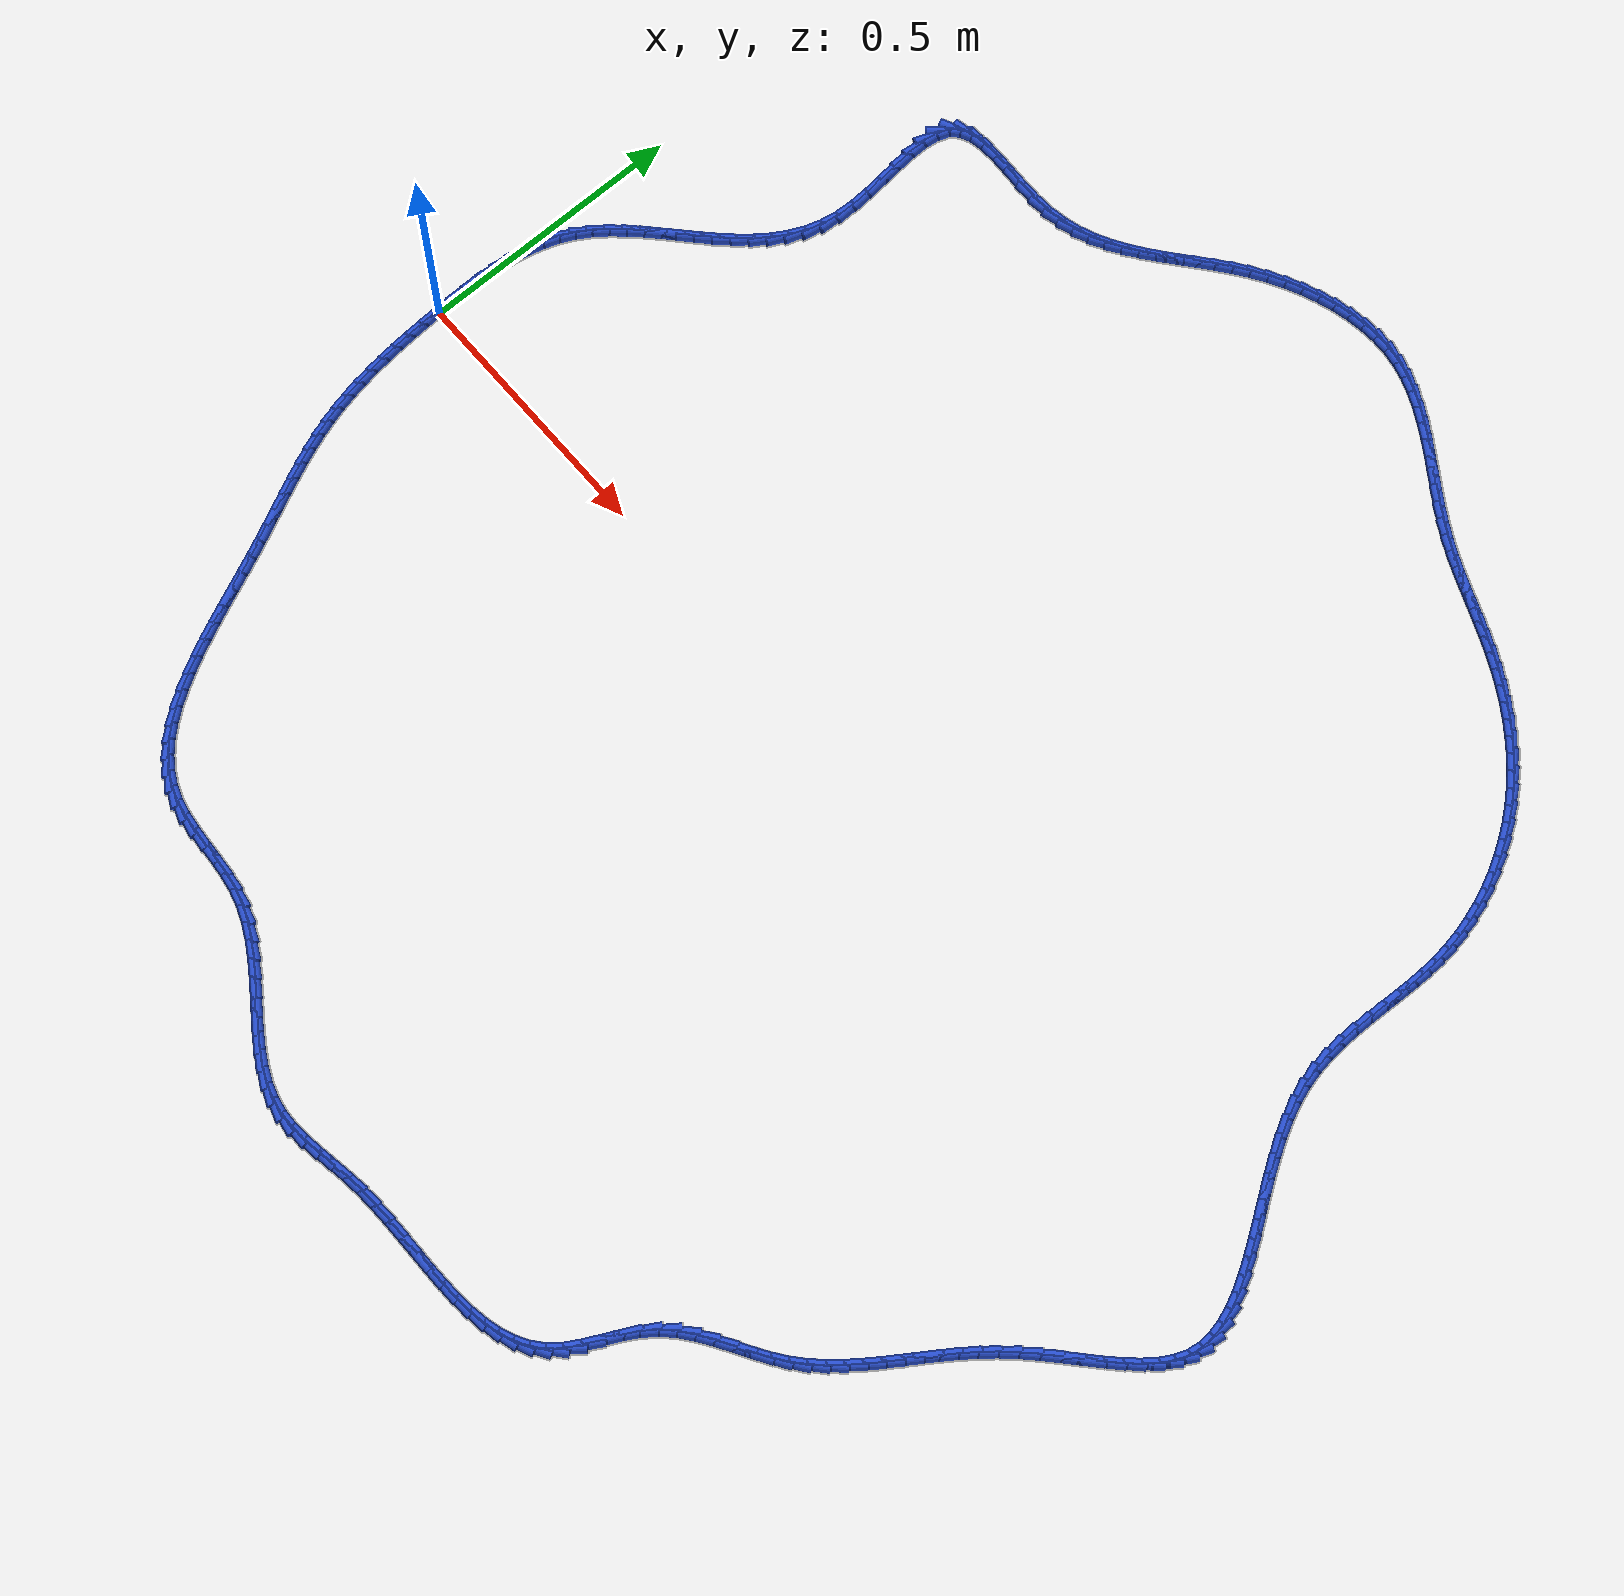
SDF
<sdf version="1.6">
 <world name="default">
  <light name="sun" type="directional">
   <pose>0 0 10 0 -0 0</pose>
   <diffuse>0.8 0.8 0.8 1</diffuse>
   <specular>0.2 0.2 0.2 1</specular>
   <attenuation>
    <range>1000</range>
    <constant>0.9</constant>
    <linear>0.01</linear>
    <quadratic>0.001</quadratic>
   </attenuation>
   <direction>-0.5 0.1 -0.9</direction>
  </light>
  <model name="ground_plane">
   <static>1</static>
   <link name="link">
    <collision name="collision">
     <geometry><plane><normal>0 0 1</normal><size>100 100</size></plane></geometry>
     <surface><friction><ode><mu>100</mu><mu2>50</mu2></ode></friction></surface>
    </collision>
    <visual name="visual">
     <cast_shadows>0</cast_shadows>
     <geometry><plane><normal>0 0 1</normal><size>100 100</size></plane></geometry>
     <material>
      <script><uri>file://media/materials/scripts/gazebo.material</uri><name>Gazebo/WhiteGlow</name></script>
     </material>
    </visual>
   </link>
  </model>
  <gravity>0 0 -9.8</gravity>
  <magnetic_field>6e-06 2.3e-05 -4.2e-05</magnetic_field>
  <atmosphere type="adiabatic"/>
  <physics name="default_physics" default="0" type="ode">
   <max_step_size>0.001</max_step_size>
   <real_time_factor>1</real_time_factor>
   <real_time_update_rate>1000</real_time_update_rate>
  </physics>
  <scene><ambient>0.4 0.4 0.4 1</ambient><background>0.7 0.7 0.7 1</background><shadows>1</shadows></scene>
  <spherical_coordinates>
   <surface_model>EARTH_WGS84</surface_model>
   <latitude_deg>0</latitude_deg>
   <longitude_deg>0</longitude_deg>
   <elevation>0</elevation>
   <heading_deg>0</heading_deg>
  </spherical_coordinates>
  <model name="line">
   <link name="link_0">
    <pose>-7.589415207398531e-18 0.0 0.01 0 1.57 -1.5366979075146932</pose>
    <collision name="collision">
     <geometry><cylinder><radius>0.01</radius><length>0.08</length></cylinder></geometry>
    </collision>
    <visual name="visual">
     <material>
      <script><name>Gazebo/Blue</name><uri>file://media/materials/scripts/gazebo.material</uri></script>
     </material>
     <geometry><cylinder><radius>0.01</radius><length>0.08</length></cylinder></geometry>
    </visual>
   </link>
   <link name="link_1">
    <pose>-0.0010923447116756582 0.03202263755056824 0.01 0 1.57 -1.5561404084608057</pose>
    <collision name="collision">
     <geometry><cylinder><radius>0.01</radius><length>0.08</length></cylinder></geometry>
    </collision>
    <visual name="visual">
     <material>
      <script><name>Gazebo/Blue</name><uri>file://media/materials/scripts/gazebo.material</uri></script>
     </material>
     <geometry><cylinder><radius>0.01</radius><length>0.08</length></cylinder></geometry>
    </visual>
   </link>
   <link name="link_2">
    <pose>-0.0015623839590746913 0.06409197514024975 0.01 0 1.57 1.5562377652178665</pose>
    <collision name="collision">
     <geometry><cylinder><radius>0.01</radius><length>0.08</length></cylinder></geometry>
    </collision>
    <visual name="visual">
     <material>
      <script><name>Gazebo/Blue</name><uri>file://media/materials/scripts/gazebo.material</uri></script>
     </material>
     <geometry><cylinder><radius>0.01</radius><length>0.08</length></cylinder></geometry>
    </visual>
   </link>
   <link name="link_3">
    <pose>-0.0010977071740875303 0.09600748769856667 0.01 0 1.57 1.5166117639212087</pose>
    <collision name="collision">
     <geometry><cylinder><radius>0.01</radius><length>0.08</length></cylinder></geometry>
    </collision>
    <visual name="visual">
     <material>
      <script><name>Gazebo/Blue</name><uri>file://media/materials/scripts/gazebo.material</uri></script>
     </material>
     <geometry><cylinder><radius>0.01</radius><length>0.08</length></cylinder></geometry>
    </visual>
   </link>
   <link name="link_4">
    <pose>0.000614096211395404 0.12756865015504104 0.01 0 1.57 1.4656794937568811</pose>
    <collision name="collision">
     <geometry><cylinder><radius>0.01</radius><length>0.08</length></cylinder></geometry>
    </collision>
    <visual name="visual">
     <material>
      <script><name>Gazebo/Blue</name><uri>file://media/materials/scripts/gazebo.material</uri></script>
     </material>
     <geometry><cylinder><radius>0.01</radius><length>0.08</length></cylinder></geometry>
    </visual>
   </link>
   <link name="link_5">
    <pose>0.0038854367654836902 0.15857493743919482 0.01 0 1.57 1.4023856880816412</pose>
    <collision name="collision">
     <geometry><cylinder><radius>0.01</radius><length>0.08</length></cylinder></geometry>
    </collision>
    <visual name="visual">
     <material>
      <script><name>Gazebo/Blue</name><uri>file://media/materials/scripts/gazebo.material</uri></script>
     </material>
     <geometry><cylinder><radius>0.01</radius><length>0.08</length></cylinder></geometry>
    </visual>
   </link>
   <link name="link_6">
    <pose>0.00902872505628691 0.18882582448055024 0.01 0 1.57 1.3256921719895018</pose>
    <collision name="collision">
     <geometry><cylinder><radius>0.01</radius><length>0.08</length></cylinder></geometry>
    </collision>
    <visual name="visual">
     <material>
      <script><name>Gazebo/Blue</name><uri>file://media/materials/scripts/gazebo.material</uri></script>
     </material>
     <geometry><cylinder><radius>0.01</radius><length>0.08</length></cylinder></geometry>
    </visual>
   </link>
   <link name="link_7">
    <pose>0.016356371651914642 0.2181207862086292 0.01 0 1.57 1.2348835637795994</pose>
    <collision name="collision">
     <geometry><cylinder><radius>0.01</radius><length>0.08</length></cylinder></geometry>
    </collision>
    <visual name="visual">
     <material>
      <script><name>Gazebo/Blue</name><uri>file://media/materials/scripts/gazebo.material</uri></script>
     </material>
     <geometry><cylinder><radius>0.01</radius><length>0.08</length></cylinder></geometry>
    </visual>
   </link>
   <link name="link_8">
    <pose>0.02618078712047646 0.24625929755295387 0.01 0 1.57 1.1300312105737216</pose>
    <collision name="collision">
     <geometry><cylinder><radius>0.01</radius><length>0.08</length></cylinder></geometry>
    </collision>
    <visual name="visual">
     <material>
      <script><name>Gazebo/Blue</name><uri>file://media/materials/scripts/gazebo.material</uri></script>
     </material>
     <geometry><cylinder><radius>0.01</radius><length>0.08</length></cylinder></geometry>
    </visual>
   </link>
   <link name="link_9">
    <pose>0.03881412423013129 0.2730409818456343 0.01 0 1.57 1.0198916303049563</pose>
    <collision name="collision">
     <geometry><cylinder><radius>0.01</radius><length>0.08</length></cylinder></geometry>
    </collision>
    <visual name="visual">
     <material>
      <script><name>Gazebo/Blue</name><uri>file://media/materials/scripts/gazebo.material</uri></script>
     </material>
     <geometry><cylinder><radius>0.01</radius><length>0.08</length></cylinder></geometry>
    </visual>
   </link>
   <link name="link_10">
    <pose>0.05437813597161116 0.29837506608501224 0.01 0 1.57 0.9269064998506293</pose>
    <collision name="collision">
     <geometry><cylinder><radius>0.01</radius><length>0.08</length></cylinder></geometry>
    </collision>
    <visual name="visual">
     <material>
      <script><name>Gazebo/Blue</name><uri>file://media/materials/scripts/gazebo.material</uri></script>
     </material>
     <geometry><cylinder><radius>0.01</radius><length>0.08</length></cylinder></geometry>
    </visual>
   </link>
   <link name="link_11">
    <pose>0.07246723397081867 0.3224743414212468 0.01 0 1.57 0.854916132959737</pose>
    <collision name="collision">
     <geometry><cylinder><radius>0.01</radius><length>0.08</length></cylinder></geometry>
    </collision>
    <visual name="visual">
     <material>
      <script><name>Gazebo/Blue</name><uri>file://media/materials/scripts/gazebo.material</uri></script>
     </material>
     <geometry><cylinder><radius>0.01</radius><length>0.08</length></cylinder></geometry>
    </visual>
   </link>
   <link name="link_12">
    <pose>0.0925852866085653 0.3456037202398714 0.01 0 1.57 0.8029463173448101</pose>
    <collision name="collision">
     <geometry><cylinder><radius>0.01</radius><length>0.08</length></cylinder></geometry>
    </collision>
    <visual name="visual">
     <material>
      <script><name>Gazebo/Blue</name><uri>file://media/materials/scripts/gazebo.material</uri></script>
     </material>
     <geometry><cylinder><radius>0.01</radius><length>0.08</length></cylinder></geometry>
    </visual>
   </link>
   <link name="link_13">
    <pose>0.11423616226566254 0.3680281149264193 0.01 0 1.57 0.7696570332971142</pose>
    <collision name="collision">
     <geometry><cylinder><radius>0.01</radius><length>0.08</length></cylinder></geometry>
    </collision>
    <visual name="visual">
     <material>
      <script><name>Gazebo/Blue</name><uri>file://media/materials/scripts/gazebo.material</uri></script>
     </material>
     <geometry><cylinder><radius>0.01</radius><length>0.08</length></cylinder></geometry>
    </visual>
   </link>
   <link name="link_14">
    <pose>0.1369237293229219 0.3900124378664239 0.01 0 1.57 0.753902173908188</pose>
    <collision name="collision">
     <geometry><cylinder><radius>0.01</radius><length>0.08</length></cylinder></geometry>
    </collision>
    <visual name="visual">
     <material>
      <script><name>Gazebo/Blue</name><uri>file://media/materials/scripts/gazebo.material</uri></script>
     </material>
     <geometry><cylinder><radius>0.01</radius><length>0.08</length></cylinder></geometry>
    </visual>
   </link>
   <link name="link_15">
    <pose>0.16015185616115493 0.4118216014454189 0.01 0 1.57 0.7549981085339544</pose>
    <collision name="collision">
     <geometry><cylinder><radius>0.01</radius><length>0.08</length></cylinder></geometry>
    </collision>
    <visual name="visual">
     <material>
      <script><name>Gazebo/Blue</name><uri>file://media/materials/scripts/gazebo.material</uri></script>
     </material>
     <geometry><cylinder><radius>0.01</radius><length>0.08</length></cylinder></geometry>
    </visual>
   </link>
   <link name="link_16">
    <pose>0.1834244111611731 0.43372051804893735 0.01 0 1.57 0.7728136551110324</pose>
    <collision name="collision">
     <geometry><cylinder><radius>0.01</radius><length>0.08</length></cylinder></geometry>
    </collision>
    <visual name="visual">
     <material>
      <script><name>Gazebo/Blue</name><uri>file://media/materials/scripts/gazebo.material</uri></script>
     </material>
     <geometry><cylinder><radius>0.01</radius><length>0.08</length></cylinder></geometry>
    </visual>
   </link>
   <link name="link_17">
    <pose>0.20624526270378798 0.4559741000625128 0.01 0 1.57 0.8077459240966005</pose>
    <collision name="collision">
     <geometry><cylinder><radius>0.01</radius><length>0.08</length></cylinder></geometry>
    </collision>
    <visual name="visual">
     <material>
      <script><name>Gazebo/Blue</name><uri>file://media/materials/scripts/gazebo.material</uri></script>
     </material>
     <geometry><cylinder><radius>0.01</radius><length>0.08</length></cylinder></geometry>
    </visual>
   </link>
   <link name="link_18">
    <pose>0.228118279169811 0.47884725987167864 0.01 0 1.57 0.8605865200698543</pose>
    <collision name="collision">
     <geometry><cylinder><radius>0.01</radius><length>0.08</length></cylinder></geometry>
    </collision>
    <visual name="visual">
     <material>
      <script><name>Gazebo/Blue</name><uri>file://media/materials/scripts/gazebo.material</uri></script>
     </material>
     <geometry><cylinder><radius>0.01</radius><length>0.08</length></cylinder></geometry>
    </visual>
   </link>
   <link name="link_19">
    <pose>0.24854732894005355 0.5026049098619679 0.01 0 1.57 0.9322299052487132</pose>
    <collision name="collision">
     <geometry><cylinder><radius>0.01</radius><length>0.08</length></cylinder></geometry>
    </collision>
    <visual name="visual">
     <material>
      <script><name>Gazebo/Blue</name><uri>file://media/materials/scripts/gazebo.material</uri></script>
     </material>
     <geometry><cylinder><radius>0.01</radius><length>0.08</length></cylinder></geometry>
    </visual>
   </link>
   <link name="link_20">
    <pose>0.2670362803953274 0.5275119624189146 0.01 0 1.57 1.0231480421252712</pose>
    <collision name="collision">
     <geometry><cylinder><radius>0.01</radius><length>0.08</length></cylinder></geometry>
    </collision>
    <visual name="visual">
     <material>
      <script><name>Gazebo/Blue</name><uri>file://media/materials/scripts/gazebo.material</uri></script>
     </material>
     <geometry><cylinder><radius>0.01</radius><length>0.08</length></cylinder></geometry>
    </visual>
   </link>
   <link name="link_21">
    <pose>0.2830890019164439 0.5538333299280518 0.01 0 1.57 1.132603800807505</pose>
    <collision name="collision">
     <geometry><cylinder><radius>0.01</radius><length>0.08</length></cylinder></geometry>
    </collision>
    <visual name="visual">
     <material>
      <script><name>Gazebo/Blue</name><uri>file://media/materials/scripts/gazebo.material</uri></script>
     </material>
     <geometry><cylinder><radius>0.01</radius><length>0.08</length></cylinder></geometry>
    </visual>
   </link>
   <link name="link_22">
    <pose>0.29620936188421465 0.581833924774913 0.01 0 1.57 1.2577782792424819</pose>
    <collision name="collision">
     <geometry><cylinder><radius>0.01</radius><length>0.08</length></cylinder></geometry>
    </collision>
    <visual name="visual">
     <material>
      <script><name>Gazebo/Blue</name><uri>file://media/materials/scripts/gazebo.material</uri></script>
     </material>
     <geometry><cylinder><radius>0.01</radius><length>0.08</length></cylinder></geometry>
    </visual>
   </link>
   <link name="link_23">
    <pose>0.305901228679451 0.6117786593450315 0.01 0 1.57 1.393319189470454</pose>
    <collision name="collision">
     <geometry><cylinder><radius>0.01</radius><length>0.08</length></cylinder></geometry>
    </collision>
    <visual name="visual">
     <material>
      <script><name>Gazebo/Blue</name><uri>file://media/materials/scripts/gazebo.material</uri></script>
     </material>
     <geometry><cylinder><radius>0.01</radius><length>0.08</length></cylinder></geometry>
    </visual>
   </link>
   <link name="link_24">
    <pose>0.3116684706829646 0.6439324460239406 0.01 0 1.57 1.52343696276558</pose>
    <collision name="collision">
     <geometry><cylinder><radius>0.01</radius><length>0.08</length></cylinder></geometry>
    </collision>
    <visual name="visual">
     <material>
      <script><name>Gazebo/Blue</name><uri>file://media/materials/scripts/gazebo.material</uri></script>
     </material>
     <geometry><cylinder><radius>0.01</radius><length>0.08</length></cylinder></geometry>
    </visual>
   </link>
   <link name="link_25">
    <pose>0.31329986506671953 0.6783538227640963 0.01 0 1.57 -1.5292156773577323</pose>
    <collision name="collision">
     <geometry><cylinder><radius>0.01</radius><length>0.08</length></cylinder></geometry>
    </collision>
    <visual name="visual">
     <material>
      <script><name>Gazebo/Blue</name><uri>file://media/materials/scripts/gazebo.material</uri></script>
     </material>
     <geometry><cylinder><radius>0.01</radius><length>0.08</length></cylinder></geometry>
    </visual>
   </link>
   <link name="link_26">
    <pose>0.31180787629895523 0.7142149464027524 0.01 0 1.57 -1.4806744450399367</pose>
    <collision name="collision">
     <geometry><cylinder><radius>0.01</radius><length>0.08</length></cylinder></geometry>
    </collision>
    <visual name="visual">
     <material>
      <script><name>Gazebo/Blue</name><uri>file://media/materials/scripts/gazebo.material</uri></script>
     </material>
     <geometry><cylinder><radius>0.01</radius><length>0.08</length></cylinder></geometry>
    </visual>
   </link>
   <link name="link_27">
    <pose>0.3085334306644922 0.7504500515954341 0.01 0 1.57 -1.4666270595807303</pose>
    <collision name="collision">
     <geometry><cylinder><radius>0.01</radius><length>0.08</length></cylinder></geometry>
    </collision>
    <visual name="visual">
     <material>
      <script><name>Gazebo/Blue</name><uri>file://media/materials/scripts/gazebo.material</uri></script>
     </material>
     <geometry><cylinder><radius>0.01</radius><length>0.08</length></cylinder></geometry>
    </visual>
   </link>
   <link name="link_28">
    <pose>0.304817458530408 0.785993370040673 0.01 0 1.57 -1.4876231146497896</pose>
    <collision name="collision">
     <geometry><cylinder><radius>0.01</radius><length>0.08</length></cylinder></geometry>
    </collision>
    <visual name="visual">
     <material>
      <script><name>Gazebo/Blue</name><uri>file://media/materials/scripts/gazebo.material</uri></script>
     </material>
     <geometry><cylinder><radius>0.01</radius><length>0.08</length></cylinder></geometry>
    </visual>
   </link>
   <link name="link_29">
    <pose>0.3020008902637805 0.8197791334370013 0.01 0 1.57 -1.5521877314463453</pose>
    <collision name="collision">
     <geometry><cylinder><radius>0.01</radius><length>0.08</length></cylinder></geometry>
    </collision>
    <visual name="visual">
     <material>
      <script><name>Gazebo/Blue</name><uri>file://media/materials/scripts/gazebo.material</uri></script>
     </material>
     <geometry><cylinder><radius>0.01</radius><length>0.08</length></cylinder></geometry>
    </visual>
   </link>
   <link name="link_30">
    <pose>0.301424656231687 0.8507415734829504 0.01 0 1.57 1.4602529168605785</pose>
    <collision name="collision">
     <geometry><cylinder><radius>0.01</radius><length>0.08</length></cylinder></geometry>
    </collision>
    <visual name="visual">
     <material>
      <script><name>Gazebo/Blue</name><uri>file://media/materials/scripts/gazebo.material</uri></script>
     </material>
     <geometry><cylinder><radius>0.01</radius><length>0.08</length></cylinder></geometry>
    </visual>
   </link>
   <link name="link_31">
    <pose>0.30442968680120536 0.877814921877053 0.01 0 1.57 1.2266595298818512</pose>
    <collision name="collision">
     <geometry><cylinder><radius>0.01</radius><length>0.08</length></cylinder></geometry>
    </collision>
    <visual name="visual">
     <material>
      <script><name>Gazebo/Blue</name><uri>file://media/materials/scripts/gazebo.material</uri></script>
     </material>
     <geometry><cylinder><radius>0.01</radius><length>0.08</length></cylinder></geometry>
    </visual>
   </link>
   <link name="link_32">
    <pose>0.312356912339413 0.8999334103178404 0.01 0 1.57 0.8486279061733764</pose>
    <collision name="collision">
     <geometry><cylinder><radius>0.01</radius><length>0.08</length></cylinder></geometry>
    </collision>
    <visual name="visual">
     <material>
      <script><name>Gazebo/Blue</name><uri>file://media/materials/scripts/gazebo.material</uri></script>
     </material>
     <geometry><cylinder><radius>0.01</radius><length>0.08</length></cylinder></geometry>
    </visual>
   </link>
   <link name="link_33">
    <pose>0.3265420439564528 0.9160361953909008 0.01 0 1.57 0.43679168437102617</pose>
    <collision name="collision">
     <geometry><cylinder><radius>0.01</radius><length>0.08</length></cylinder></geometry>
    </collision>
    <visual name="visual">
     <material>
      <script><name>Gazebo/Blue</name><uri>file://media/materials/scripts/gazebo.material</uri></script>
     </material>
     <geometry><cylinder><radius>0.01</radius><length>0.08</length></cylinder></geometry>
    </visual>
   </link>
   <link name="link_34">
    <pose>0.34751145643737574 0.9258261228509707 0.01 0 1.57 0.1771759746403621</pose>
    <collision name="collision">
     <geometry><cylinder><radius>0.01</radius><length>0.08</length></cylinder></geometry>
    </collision>
    <visual name="visual">
     <material>
      <script><name>Gazebo/Blue</name><uri>file://media/materials/scripts/gazebo.material</uri></script>
     </material>
     <geometry><cylinder><radius>0.01</radius><length>0.08</length></cylinder></geometry>
    </visual>
   </link>
   <link name="link_35">
    <pose>0.37411359781994674 0.9305893289141138 0.01 0 1.57 0.03947198610408888</pose>
    <collision name="collision">
     <geometry><cylinder><radius>0.01</radius><length>0.08</length></cylinder></geometry>
    </collision>
    <visual name="visual">
     <material>
      <script><name>Gazebo/Blue</name><uri>file://media/materials/scripts/gazebo.material</uri></script>
     </material>
     <geometry><cylinder><radius>0.01</radius><length>0.08</length></cylinder></geometry>
    </visual>
   </link>
   <link name="link_36">
    <pose>0.40498845440354697 0.9318086541414848 0.01 0 1.57 -0.024906830652062367</pose>
    <collision name="collision">
     <geometry><cylinder><radius>0.01</radius><length>0.08</length></cylinder></geometry>
    </collision>
    <visual name="visual">
     <material>
      <script><name>Gazebo/Blue</name><uri>file://media/materials/scripts/gazebo.material</uri></script>
     </material>
     <geometry><cylinder><radius>0.01</radius><length>0.08</length></cylinder></geometry>
    </visual>
   </link>
   <link name="link_37">
    <pose>0.4387760124875581 0.930966939094238 0.01 0 1.57 -0.04015680723872802</pose>
    <collision name="collision">
     <geometry><cylinder><radius>0.01</radius><length>0.08</length></cylinder></geometry>
    </collision>
    <visual name="visual">
     <material>
      <script><name>Gazebo/Blue</name><uri>file://media/materials/scripts/gazebo.material</uri></script>
     </material>
     <geometry><cylinder><radius>0.01</radius><length>0.08</length></cylinder></geometry>
    </visual>
   </link>
   <link name="link_38">
    <pose>0.47411625837136084 0.9295470243335275 0.01 0 1.57 -0.01450029435183917</pose>
    <collision name="collision">
     <geometry><cylinder><radius>0.01</radius><length>0.08</length></cylinder></geometry>
    </collision>
    <visual name="visual">
     <material>
      <script><name>Gazebo/Blue</name><uri>file://media/materials/scripts/gazebo.material</uri></script>
     </material>
     <geometry><cylinder><radius>0.01</radius><length>0.08</length></cylinder></geometry>
    </visual>
   </link>
   <link name="link_39">
    <pose>0.5096491783543373 0.9290317504205082 0.01 0 1.57 0.05441502153179256</pose>
    <collision name="collision">
     <geometry><cylinder><radius>0.01</radius><length>0.08</length></cylinder></geometry>
    </collision>
    <visual name="visual">
     <material>
      <script><name>Gazebo/Blue</name><uri>file://media/materials/scripts/gazebo.material</uri></script>
     </material>
     <geometry><cylinder><radius>0.01</radius><length>0.08</length></cylinder></geometry>
    </visual>
   </link>
   <link name="link_40">
    <pose>0.5440150556973586 0.9309036182710717 0.01 0 1.57 0.16369060617507925</pose>
    <collision name="collision">
     <geometry><cylinder><radius>0.01</radius><length>0.08</length></cylinder></geometry>
    </collision>
    <visual name="visual">
     <material>
      <script><name>Gazebo/Blue</name><uri>file://media/materials/scripts/gazebo.material</uri></script>
     </material>
     <geometry><cylinder><radius>0.01</radius><length>0.08</length></cylinder></geometry>
    </visual>
   </link>
   <link name="link_41">
    <pose>0.5762229499386853 0.936223346449041 0.01 0 1.57 0.2773982860629447</pose>
    <collision name="collision">
     <geometry><cylinder><radius>0.01</radius><length>0.08</length></cylinder></geometry>
    </collision>
    <visual name="visual">
     <material>
      <script><name>Gazebo/Blue</name><uri>file://media/materials/scripts/gazebo.material</uri></script>
     </material>
     <geometry><cylinder><radius>0.01</radius><length>0.08</length></cylinder></geometry>
    </visual>
   </link>
   <link name="link_42">
    <pose>0.6063698418677874 0.9448073598574593 0.01 0 1.57 0.3830366115178532</pose>
    <collision name="collision">
     <geometry><cylinder><radius>0.01</radius><length>0.08</length></cylinder></geometry>
    </collision>
    <visual name="visual">
     <material>
      <script><name>Gazebo/Blue</name><uri>file://media/materials/scripts/gazebo.material</uri></script>
     </material>
     <geometry><cylinder><radius>0.01</radius><length>0.08</length></cylinder></geometry>
    </visual>
   </link>
   <link name="link_43">
    <pose>0.6347523489316713 0.9562437519579621 0.01 0 1.57 0.4760385590974551</pose>
    <collision name="collision">
     <geometry><cylinder><radius>0.01</radius><length>0.08</length></cylinder></geometry>
    </collision>
    <visual name="visual">
     <material>
      <script><name>Gazebo/Blue</name><uri>file://media/materials/scripts/gazebo.material</uri></script>
     </material>
     <geometry><cylinder><radius>0.01</radius><length>0.08</length></cylinder></geometry>
    </visual>
   </link>
   <link name="link_44">
    <pose>0.6616670885773418 0.9701206162121828 0.01 0 1.57 0.5534342682229622</pose>
    <collision name="collision">
     <geometry><cylinder><radius>0.01</radius><length>0.08</length></cylinder></geometry>
    </collision>
    <visual name="visual">
     <material>
      <script><name>Gazebo/Blue</name><uri>file://media/materials/scripts/gazebo.material</uri></script>
     </material>
     <geometry><cylinder><radius>0.01</radius><length>0.08</length></cylinder></geometry>
    </visual>
   </link>
   <link name="link_45">
    <pose>0.6874106782518049 0.9860260460817564 0.01 0 1.57 0.6137891139172305</pose>
    <collision name="collision">
     <geometry><cylinder><radius>0.01</radius><length>0.08</length></cylinder></geometry>
    </collision>
    <visual name="visual">
     <material>
      <script><name>Gazebo/Blue</name><uri>file://media/materials/scripts/gazebo.material</uri></script>
     </material>
     <geometry><cylinder><radius>0.01</radius><length>0.08</length></cylinder></geometry>
    </visual>
   </link>
   <link name="link_46">
    <pose>0.7122797354020655 1.0035481350283162 0.01 0 1.57 0.6567641380929898</pose>
    <collision name="collision">
     <geometry><cylinder><radius>0.01</radius><length>0.08</length></cylinder></geometry>
    </collision>
    <visual name="visual">
     <material>
      <script><name>Gazebo/Blue</name><uri>file://media/materials/scripts/gazebo.material</uri></script>
     </material>
     <geometry><cylinder><radius>0.01</radius><length>0.08</length></cylinder></geometry>
    </visual>
   </link>
   <link name="link_47">
    <pose>0.7365708774751294 1.022274976513497 0.01 0 1.57 0.6826097325852077</pose>
    <collision name="collision">
     <geometry><cylinder><radius>0.01</radius><length>0.08</length></cylinder></geometry>
    </collision>
    <visual name="visual">
     <material>
      <script><name>Gazebo/Blue</name><uri>file://media/materials/scripts/gazebo.material</uri></script>
     </material>
     <geometry><cylinder><radius>0.01</radius><length>0.08</length></cylinder></geometry>
    </visual>
   </link>
   <link name="link_48">
    <pose>0.7605807219180021 1.041794663998933 0.01 0 1.57 0.6917748233320972</pose>
    <collision name="collision">
     <geometry><cylinder><radius>0.01</radius><length>0.08</length></cylinder></geometry>
    </collision>
    <visual name="visual">
     <material>
      <script><name>Gazebo/Blue</name><uri>file://media/materials/scripts/gazebo.material</uri></script>
     </material>
     <geometry><cylinder><radius>0.01</radius><length>0.08</length></cylinder></geometry>
    </visual>
   </link>
   <link name="link_49">
    <pose>0.7846058861776888 1.061695290946258 0.01 0 1.57 0.6846822135992061</pose>
    <collision name="collision">
     <geometry><cylinder><radius>0.01</radius><length>0.08</length></cylinder></geometry>
    </collision>
    <visual name="visual">
     <material>
      <script><name>Gazebo/Blue</name><uri>file://media/materials/scripts/gazebo.material</uri></script>
     </material>
     <geometry><cylinder><radius>0.01</radius><length>0.08</length></cylinder></geometry>
    </visual>
   </link>
   <link name="link_50">
    <pose>0.8089429877011953 1.0815649508171068 0.01 0 1.57 0.661657547804356</pose>
    <collision name="collision">
     <geometry><cylinder><radius>0.01</radius><length>0.08</length></cylinder></geometry>
    </collision>
    <visual name="visual">
     <material>
      <script><name>Gazebo/Blue</name><uri>file://media/materials/scripts/gazebo.material</uri></script>
     </material>
     <geometry><cylinder><radius>0.01</radius><length>0.08</length></cylinder></geometry>
    </visual>
   </link>
   <link name="link_51">
    <pose>0.8338886439355269 1.1009917370731137 0.01 0 1.57 0.6229881840556644</pose>
    <collision name="collision">
     <geometry><cylinder><radius>0.01</radius><length>0.08</length></cylinder></geometry>
    </collision>
    <visual name="visual">
     <material>
      <script><name>Gazebo/Blue</name><uri>file://media/materials/scripts/gazebo.material</uri></script>
     </material>
     <geometry><cylinder><radius>0.01</radius><length>0.08</length></cylinder></geometry>
    </visual>
   </link>
   <link name="link_52">
    <pose>0.8597394723276888 1.1195637431759116 0.01 0 1.57 0.5698108738158983</pose>
    <collision name="collision">
     <geometry><cylinder><radius>0.01</radius><length>0.08</length></cylinder></geometry>
    </collision>
    <visual name="visual">
     <material>
      <script><name>Gazebo/Blue</name><uri>file://media/materials/scripts/gazebo.material</uri></script>
     </material>
     <geometry><cylinder><radius>0.01</radius><length>0.08</length></cylinder></geometry>
    </visual>
   </link>
   <link name="link_53">
    <pose>0.886765340036985 1.1368792641053522 0.01 0 1.57 0.5104150709255817</pose>
    <collision name="collision">
     <geometry><cylinder><radius>0.01</radius><length>0.08</length></cylinder></geometry>
    </collision>
    <visual name="visual">
     <material>
      <script><name>Gazebo/Blue</name><uri>file://media/materials/scripts/gazebo.material</uri></script>
     </material>
     <geometry><cylinder><radius>0.01</radius><length>0.08</length></cylinder></geometry>
    </visual>
   </link>
   <link name="link_54">
    <pose>0.9149348564074614 1.1526514828426513 0.01 0 1.57 0.4489262834717283</pose>
    <collision name="collision">
     <geometry><cylinder><radius>0.01</radius><length>0.08</length></cylinder></geometry>
    </collision>
    <visual name="visual">
     <material>
      <script><name>Gazebo/Blue</name><uri>file://media/materials/scripts/gazebo.material</uri></script>
     </material>
     <geometry><cylinder><radius>0.01</radius><length>0.08</length></cylinder></geometry>
    </visual>
   </link>
   <link name="link_55">
    <pose>0.9440267863431491 1.1666659816469163 0.01 0 1.57 0.38418868727455163</pose>
    <collision name="collision">
     <geometry><cylinder><radius>0.01</radius><length>0.08</length></cylinder></geometry>
    </collision>
    <visual name="visual">
     <material>
      <script><name>Gazebo/Blue</name><uri>file://media/materials/scripts/gazebo.material</uri></script>
     </material>
     <geometry><cylinder><radius>0.01</radius><length>0.08</length></cylinder></geometry>
    </visual>
   </link>
   <link name="link_56">
    <pose>0.9738169274932803 1.1787094743727071 0.01 0 1.57 0.3149296244148767</pose>
    <collision name="collision">
     <geometry><cylinder><radius>0.01</radius><length>0.08</length></cylinder></geometry>
    </collision>
    <visual name="visual">
     <material>
      <script><name>Gazebo/Blue</name><uri>file://media/materials/scripts/gazebo.material</uri></script>
     </material>
     <geometry><cylinder><radius>0.01</radius><length>0.08</length></cylinder></geometry>
    </visual>
   </link>
   <link name="link_57">
    <pose>1.0040810775070872 1.1885686748745825 0.01 0 1.57 0.2398252100839454</pose>
    <collision name="collision">
     <geometry><cylinder><radius>0.01</radius><length>0.08</length></cylinder></geometry>
    </collision>
    <visual name="visual">
     <material>
      <script><name>Gazebo/Blue</name><uri>file://media/materials/scripts/gazebo.material</uri></script>
     </material>
     <geometry><cylinder><radius>0.01</radius><length>0.08</length></cylinder></geometry>
    </visual>
   </link>
   <link name="link_58">
    <pose>1.0345950340338022 1.1960302970071013 0.01 0 1.57 0.15751934321451455</pose>
    <collision name="collision">
     <geometry><cylinder><radius>0.01</radius><length>0.08</length></cylinder></geometry>
    </collision>
    <visual name="visual">
     <material>
      <script><name>Gazebo/Blue</name><uri>file://media/materials/scripts/gazebo.material</uri></script>
     </material>
     <geometry><cylinder><radius>0.01</radius><length>0.08</length></cylinder></geometry>
    </visual>
   </link>
   <link name="link_59">
    <pose>1.0651345947226571 1.2008810546248219 0.01 0 1.57 0.06669534960263131</pose>
    <collision name="collision">
     <geometry><cylinder><radius>0.01</radius><length>0.08</length></cylinder></geometry>
    </collision>
    <visual name="visual">
     <material>
      <script><name>Gazebo/Blue</name><uri>file://media/materials/scripts/gazebo.material</uri></script>
     </material>
     <geometry><cylinder><radius>0.01</radius><length>0.08</length></cylinder></geometry>
    </visual>
   </link>
   <link name="link_60">
    <pose>1.095475557222885 1.202907661582305 0.01 0 1.57 -0.03377364835423569</pose>
    <collision name="collision">
     <geometry><cylinder><radius>0.01</radius><length>0.08</length></cylinder></geometry>
    </collision>
    <visual name="visual">
     <material>
      <script><name>Gazebo/Blue</name><uri>file://media/materials/scripts/gazebo.material</uri></script>
     </material>
     <geometry><cylinder><radius>0.01</radius><length>0.08</length></cylinder></geometry>
    </visual>
   </link>
   <link name="link_61">
    <pose>1.1253937191837178 1.2018968317341083 0.01 0 1.57 -0.14431171110946056</pose>
    <collision name="collision">
     <geometry><cylinder><radius>0.01</radius><length>0.08</length></cylinder></geometry>
    </collision>
    <visual name="visual">
     <material>
      <script><name>Gazebo/Blue</name><uri>file://media/materials/scripts/gazebo.material</uri></script>
     </material>
     <geometry><cylinder><radius>0.01</radius><length>0.08</length></cylinder></geometry>
    </visual>
   </link>
   <link name="link_62">
    <pose>1.1546686072818466 1.1976425484047333 0.01 0 1.57 -0.2545763938784624</pose>
    <collision name="collision">
     <geometry><cylinder><radius>0.01</radius><length>0.08</length></cylinder></geometry>
    </collision>
    <visual name="visual">
     <material>
      <script><name>Gazebo/Blue</name><uri>file://media/materials/scripts/gazebo.material</uri></script>
     </material>
     <geometry><cylinder><radius>0.01</radius><length>0.08</length></cylinder></geometry>
    </visual>
   </link>
   <link name="link_63">
    <pose>1.1832202850649123 1.190212761407325 0.01 0 1.57 -0.3497358407447202</pose>
    <collision name="collision">
     <geometry><cylinder><radius>0.01</radius><length>0.08</length></cylinder></geometry>
    </collision>
    <visual name="visual">
     <material>
      <script><name>Gazebo/Blue</name><uri>file://media/materials/scripts/gazebo.material</uri></script>
     </material>
     <geometry><cylinder><radius>0.01</radius><length>0.08</length></cylinder></geometry>
    </visual>
   </link>
   <link name="link_64">
    <pose>1.2111488567032964 1.1800263967571685 0.01 0 1.57 -0.42779413349664697</pose>
    <collision name="collision">
     <geometry><cylinder><radius>0.01</radius><length>0.08</length></cylinder></geometry>
    </collision>
    <visual name="visual">
     <material>
      <script><name>Gazebo/Blue</name><uri>file://media/materials/scripts/gazebo.material</uri></script>
     </material>
     <geometry><cylinder><radius>0.01</radius><length>0.08</length></cylinder></geometry>
    </visual>
   </link>
   <link name="link_65">
    <pose>1.2385662084310867 1.1675253487525383 0.01 0 1.57 -0.4889259432721871</pose>
    <collision name="collision">
     <geometry><cylinder><radius>0.01</radius><length>0.08</length></cylinder></geometry>
    </collision>
    <visual name="visual">
     <material>
      <script><name>Gazebo/Blue</name><uri>file://media/materials/scripts/gazebo.material</uri></script>
     </material>
     <geometry><cylinder><radius>0.01</radius><length>0.08</length></cylinder></geometry>
    </visual>
   </link>
   <link name="link_66">
    <pose>1.265584226482372 1.1531515116917097 0.01 0 1.57 -0.5339686493828901</pose>
    <collision name="collision">
     <geometry><cylinder><radius>0.01</radius><length>0.08</length></cylinder></geometry>
    </collision>
    <visual name="visual">
     <material>
      <script><name>Gazebo/Blue</name><uri>file://media/materials/scripts/gazebo.material</uri></script>
     </material>
     <geometry><cylinder><radius>0.01</radius><length>0.08</length></cylinder></geometry>
    </visual>
   </link>
   <link name="link_67">
    <pose>1.2923147970912394 1.1373467798729577 0.01 0 1.57 -0.5639122370377647</pose>
    <collision name="collision">
     <geometry><cylinder><radius>0.01</radius><length>0.08</length></cylinder></geometry>
    </collision>
    <visual name="visual">
     <material>
      <script><name>Gazebo/Blue</name><uri>file://media/materials/scripts/gazebo.material</uri></script>
     </material>
     <geometry><cylinder><radius>0.01</radius><length>0.08</length></cylinder></geometry>
    </visual>
   </link>
   <link name="link_68">
    <pose>1.3188698064917777 1.1205530475945573 0.01 0 1.57 -0.5795918885365203</pose>
    <collision name="collision">
     <geometry><cylinder><radius>0.01</radius><length>0.08</length></cylinder></geometry>
    </collision>
    <visual name="visual">
     <material>
      <script><name>Gazebo/Blue</name><uri>file://media/materials/scripts/gazebo.material</uri></script>
     </material>
     <geometry><cylinder><radius>0.01</radius><length>0.08</length></cylinder></geometry>
    </visual>
   </link>
   <link name="link_69">
    <pose>1.3453611409180746 1.1032122091547836 0.01 0 1.57 -0.5815322048873945</pose>
    <collision name="collision">
     <geometry><cylinder><radius>0.01</radius><length>0.08</length></cylinder></geometry>
    </collision>
    <visual name="visual">
     <material>
      <script><name>Gazebo/Blue</name><uri>file://media/materials/scripts/gazebo.material</uri></script>
     </material>
     <geometry><cylinder><radius>0.01</radius><length>0.08</length></cylinder></geometry>
    </visual>
   </link>
   <link name="link_70">
    <pose>1.3719006866042183 1.0857661588519119 0.01 0 1.57 -0.5698868016549801</pose>
    <collision name="collision">
     <geometry><cylinder><radius>0.01</radius><length>0.08</length></cylinder></geometry>
    </collision>
    <visual name="visual">
     <material>
      <script><name>Gazebo/Blue</name><uri>file://media/materials/scripts/gazebo.material</uri></script>
     </material>
     <geometry><cylinder><radius>0.01</radius><length>0.08</length></cylinder></geometry>
    </visual>
   </link>
   <link name="link_71">
    <pose>1.3986003297842966 1.068656790984217 0.01 0 1.57 -0.5444394563425698</pose>
    <collision name="collision">
     <geometry><cylinder><radius>0.01</radius><length>0.08</length></cylinder></geometry>
    </collision>
    <visual name="visual">
     <material>
      <script><name>Gazebo/Blue</name><uri>file://media/materials/scripts/gazebo.material</uri></script>
     </material>
     <geometry><cylinder><radius>0.01</radius><length>0.08</length></cylinder></geometry>
    </visual>
   </link>
   <link name="link_72">
    <pose>1.4255719566923981 1.052325999849974 0.01 0 1.57 -0.5047392713394546</pose>
    <collision name="collision">
     <geometry><cylinder><radius>0.01</radius><length>0.08</length></cylinder></geometry>
    </collision>
    <visual name="visual">
     <material>
      <script><name>Gazebo/Blue</name><uri>file://media/materials/scripts/gazebo.material</uri></script>
     </material>
     <geometry><cylinder><radius>0.01</radius><length>0.08</length></cylinder></geometry>
    </visual>
   </link>
   <link name="link_73">
    <pose>1.4529267526491638 1.037213235554282 0.01 0 1.57 -0.4585980168633063</pose>
    <collision name="collision">
     <geometry><cylinder><radius>0.01</radius><length>0.08</length></cylinder></geometry>
    </collision>
    <visual name="visual">
     <material>
      <script><name>Gazebo/Blue</name><uri>file://media/materials/scripts/gazebo.material</uri></script>
     </material>
     <geometry><cylinder><radius>0.01</radius><length>0.08</length></cylinder></geometry>
    </visual>
   </link>
   <link name="link_74">
    <pose>1.4807020632485124 1.0235004576986149 0.01 0 1.57 -0.42192605350317947</pose>
    <collision name="collision">
     <geometry><cylinder><radius>0.01</radius><length>0.08</length></cylinder></geometry>
    </collision>
    <visual name="visual">
     <material>
      <script><name>Gazebo/Blue</name><uri>file://media/materials/scripts/gazebo.material</uri></script>
     </material>
     <geometry><cylinder><radius>0.01</radius><length>0.08</length></cylinder></geometry>
    </visual>
   </link>
   <link name="link_75">
    <pose>1.5087973780832349 1.010888900768964 0.01 0 1.57 -0.3969021513975742</pose>
    <collision name="collision">
     <geometry><cylinder><radius>0.01</radius><length>0.08</length></cylinder></geometry>
    </collision>
    <visual name="visual">
     <material>
      <script><name>Gazebo/Blue</name><uri>file://media/materials/scripts/gazebo.material</uri></script>
     </material>
     <geometry><cylinder><radius>0.01</radius><length>0.08</length></cylinder></geometry>
    </visual>
   </link>
   <link name="link_76">
    <pose>1.5370970962316524 0.9990271763023538 0.01 0 1.57 -0.3837778156022704</pose>
    <collision name="collision">
     <geometry><cylinder><radius>0.01</radius><length>0.08</length></cylinder></geometry>
    </collision>
    <visual name="visual">
     <material>
      <script><name>Gazebo/Blue</name><uri>file://media/materials/scripts/gazebo.material</uri></script>
     </material>
     <geometry><cylinder><radius>0.01</radius><length>0.08</length></cylinder></geometry>
    </visual>
   </link>
   <link name="link_77">
    <pose>1.5654856167720879 0.987563895835809 0.01 0 1.57 -0.38267886107966387</pose>
    <collision name="collision">
     <geometry><cylinder><radius>0.01</radius><length>0.08</length></cylinder></geometry>
    </collision>
    <visual name="visual">
     <material>
      <script><name>Gazebo/Blue</name><uri>file://media/materials/scripts/gazebo.material</uri></script>
     </material>
     <geometry><cylinder><radius>0.01</radius><length>0.08</length></cylinder></geometry>
    </visual>
   </link>
   <link name="link_78">
    <pose>1.5938473387828602 0.9761476709063533 0.01 0 1.57 -0.3936584936075167</pose>
    <collision name="collision">
     <geometry><cylinder><radius>0.01</radius><length>0.08</length></cylinder></geometry>
    </collision>
    <visual name="visual">
     <material>
      <script><name>Gazebo/Blue</name><uri>file://media/materials/scripts/gazebo.material</uri></script>
     </material>
     <geometry><cylinder><radius>0.01</radius><length>0.08</length></cylinder></geometry>
    </visual>
   </link>
   <link name="link_79">
    <pose>1.6220666613422914 0.9644271130510104 0.01 0 1.57 -0.4167009541719072</pose>
    <collision name="collision">
     <geometry><cylinder><radius>0.01</radius><length>0.08</length></cylinder></geometry>
    </collision>
    <visual name="visual">
     <material>
      <script><name>Gazebo/Blue</name><uri>file://media/materials/scripts/gazebo.material</uri></script>
     </material>
     <geometry><cylinder><radius>0.01</radius><length>0.08</length></cylinder></geometry>
    </visual>
   </link>
   <link name="link_80">
    <pose>1.6500279835287033 0.9520508338068054 0.01 0 1.57 -0.45145092223446137</pose>
    <collision name="collision">
     <geometry><cylinder><radius>0.01</radius><length>0.08</length></cylinder></geometry>
    </collision>
    <visual name="visual">
     <material>
      <script><name>Gazebo/Blue</name><uri>file://media/materials/scripts/gazebo.material</uri></script>
     </material>
     <geometry><cylinder><radius>0.01</radius><length>0.08</length></cylinder></geometry>
    </visual>
   </link>
   <link name="link_81">
    <pose>1.6776159340828787 0.9386749316962268 0.01 0 1.57 -0.4927703629924155</pose>
    <collision name="collision">
     <geometry><cylinder><radius>0.01</radius><length>0.08</length></cylinder></geometry>
    </collision>
    <visual name="visual">
     <material>
      <script><name>Gazebo/Blue</name><uri>file://media/materials/scripts/gazebo.material</uri></script>
     </material>
     <geometry><cylinder><radius>0.01</radius><length>0.08</length></cylinder></geometry>
    </visual>
   </link>
   <link name="link_82">
    <pose>1.7047202253148814 0.9241212293604488 0.01 0 1.57 -0.535922900961422</pose>
    <collision name="collision">
     <geometry><cylinder><radius>0.01</radius><length>0.08</length></cylinder></geometry>
    </collision>
    <visual name="visual">
     <material>
      <script><name>Gazebo/Blue</name><uri>file://media/materials/scripts/gazebo.material</uri></script>
     </material>
     <geometry><cylinder><radius>0.01</radius><length>0.08</length></cylinder></geometry>
    </visual>
   </link>
   <link name="link_83">
    <pose>1.7312355451231782 0.9083737533878852 0.01 0 1.57 -0.5808984180801068</pose>
    <collision name="collision">
     <geometry><cylinder><radius>0.01</radius><length>0.08</length></cylinder></geometry>
    </collision>
    <visual name="visual">
     <material>
      <script><name>Gazebo/Blue</name><uri>file://media/materials/scripts/gazebo.material</uri></script>
     </material>
     <geometry><cylinder><radius>0.01</radius><length>0.08</length></cylinder></geometry>
    </visual>
   </link>
   <link name="link_84">
    <pose>1.7570567894694027 0.8914233132163893 0.01 0 1.57 -0.6278737316190417</pose>
    <collision name="collision">
     <geometry><cylinder><radius>0.01</radius><length>0.08</length></cylinder></geometry>
    </collision>
    <visual name="visual">
     <material>
      <script><name>Gazebo/Blue</name><uri>file://media/materials/scripts/gazebo.material</uri></script>
     </material>
     <geometry><cylinder><radius>0.01</radius><length>0.08</length></cylinder></geometry>
    </visual>
   </link>
   <link name="link_85">
    <pose>1.7820788543151886 0.873260718283814 0.01 0 1.57 -0.677005048405355</pose>
    <collision name="collision">
     <geometry><cylinder><radius>0.01</radius><length>0.08</length></cylinder></geometry>
    </collision>
    <visual name="visual">
     <material>
      <script><name>Gazebo/Blue</name><uri>file://media/materials/scripts/gazebo.material</uri></script>
     </material>
     <geometry><cylinder><radius>0.01</radius><length>0.08</length></cylinder></geometry>
    </visual>
   </link>
   <link name="link_86">
    <pose>1.80619663562217 0.8538767780280131 0.01 0 1.57 -0.7284206997887859</pose>
    <collision name="collision">
     <geometry><cylinder><radius>0.01</radius><length>0.08</length></cylinder></geometry>
    </collision>
    <visual name="visual">
     <material>
      <script><name>Gazebo/Blue</name><uri>file://media/materials/scripts/gazebo.material</uri></script>
     </material>
     <geometry><cylinder><radius>0.01</radius><length>0.08</length></cylinder></geometry>
    </visual>
   </link>
   <link name="link_87">
    <pose>1.8293050293519801 0.8332623018868393 0.01 0 1.57 -0.7822121864013021</pose>
    <collision name="collision">
     <geometry><cylinder><radius>0.01</radius><length>0.08</length></cylinder></geometry>
    </collision>
    <visual name="visual">
     <material>
      <script><name>Gazebo/Blue</name><uri>file://media/materials/scripts/gazebo.material</uri></script>
     </material>
     <geometry><cylinder><radius>0.01</radius><length>0.08</length></cylinder></geometry>
    </visual>
   </link>
   <link name="link_88">
    <pose>1.8512989314662538 0.8114080992981452 0.01 0 1.57 -0.838423836945611</pose>
    <collision name="collision">
     <geometry><cylinder><radius>0.01</radius><length>0.08</length></cylinder></geometry>
    </collision>
    <visual name="visual">
     <material>
      <script><name>Gazebo/Blue</name><uri>file://media/materials/scripts/gazebo.material</uri></script>
     </material>
     <geometry><cylinder><radius>0.01</radius><length>0.08</length></cylinder></geometry>
    </visual>
   </link>
   <link name="link_89">
    <pose>1.8720732379266243 0.7883049796997851 0.01 0 1.57 -0.8968084459973062</pose>
    <collision name="collision">
     <geometry><cylinder><radius>0.01</radius><length>0.08</length></cylinder></geometry>
    </collision>
    <visual name="visual">
     <material>
      <script><name>Gazebo/Blue</name><uri>file://media/materials/scripts/gazebo.material</uri></script>
     </material>
     <geometry><cylinder><radius>0.01</radius><length>0.08</length></cylinder></geometry>
    </visual>
   </link>
   <link name="link_90">
    <pose>1.8915239523201701 0.763954016904576 0.01 0 1.57 -0.9555890569865575</pose>
    <collision name="collision">
     <geometry><cylinder><radius>0.01</radius><length>0.08</length></cylinder></geometry>
    </collision>
    <visual name="visual">
     <material>
      <script><name>Gazebo/Blue</name><uri>file://media/materials/scripts/gazebo.material</uri></script>
     </material>
     <geometry><cylinder><radius>0.01</radius><length>0.08</length></cylinder></geometry>
    </visual>
   </link>
   <link name="link_91">
    <pose>1.90955591987808 0.7384382203208998 0.01 0 1.57 -1.0142760520478078</pose>
    <collision name="collision">
     <geometry><cylinder><radius>0.01</radius><length>0.08</length></cylinder></geometry>
    </collision>
    <visual name="visual">
     <material>
      <script><name>Gazebo/Blue</name><uri>file://media/materials/scripts/gazebo.material</uri></script>
     </material>
     <geometry><cylinder><radius>0.01</radius><length>0.08</length></cylinder></geometry>
    </visual>
   </link>
   <link name="link_92">
    <pose>1.9260782205953082 0.7118798429510499 0.01 0 1.57 -1.0733169394948778</pose>
    <collision name="collision">
     <geometry><cylinder><radius>0.01</radius><length>0.08</length></cylinder></geometry>
    </collision>
    <visual name="visual">
     <material>
      <script><name>Gazebo/Blue</name><uri>file://media/materials/scripts/gazebo.material</uri></script>
     </material>
     <geometry><cylinder><radius>0.01</radius><length>0.08</length></cylinder></geometry>
    </visual>
   </link>
   <link name="link_93">
    <pose>1.9409999610129212 0.6844013838004184 0.01 0 1.57 -1.133159000432719</pose>
    <collision name="collision">
     <geometry><cylinder><radius>0.01</radius><length>0.08</length></cylinder></geometry>
    </collision>
    <visual name="visual">
     <material>
      <script><name>Gazebo/Blue</name><uri>file://media/materials/scripts/gazebo.material</uri></script>
     </material>
     <geometry><cylinder><radius>0.01</radius><length>0.08</length></cylinder></geometry>
    </visual>
   </link>
   <link name="link_94">
    <pose>1.9542302476719888 0.6561253418743968 0.01 0 1.57 -1.1942419018317</pose>
    <collision name="collision">
     <geometry><cylinder><radius>0.01</radius><length>0.08</length></cylinder></geometry>
    </collision>
    <visual name="visual">
     <material>
      <script><name>Gazebo/Blue</name><uri>file://media/materials/scripts/gazebo.material</uri></script>
     </material>
     <geometry><cylinder><radius>0.01</radius><length>0.08</length></cylinder></geometry>
    </visual>
   </link>
   <link name="link_95">
    <pose>1.9656781871135804 0.6271742161783778 0.01 0 1.57 -1.2569938903587312</pose>
    <collision name="collision">
     <geometry><cylinder><radius>0.01</radius><length>0.08</length></cylinder></geometry>
    </collision>
    <visual name="visual">
     <material>
      <script><name>Gazebo/Blue</name><uri>file://media/materials/scripts/gazebo.material</uri></script>
     </material>
     <geometry><cylinder><radius>0.01</radius><length>0.08</length></cylinder></geometry>
    </visual>
   </link>
   <link name="link_96">
    <pose>1.975252885878764 0.5976705057177523 0.01 0 1.57 -1.3218249147971985</pose>
    <collision name="collision">
     <geometry><cylinder><radius>0.01</radius><length>0.08</length></cylinder></geometry>
    </collision>
    <visual name="visual">
     <material>
      <script><name>Gazebo/Blue</name><uri>file://media/materials/scripts/gazebo.material</uri></script>
     </material>
     <geometry><cylinder><radius>0.01</radius><length>0.08</length></cylinder></geometry>
    </visual>
   </link>
   <link name="link_97">
    <pose>1.982863450508608 0.5677367094979131 0.01 0 1.57 -1.3891155950454888</pose>
    <collision name="collision">
     <geometry><cylinder><radius>0.01</radius><length>0.08</length></cylinder></geometry>
    </collision>
    <visual name="visual">
     <material>
      <script><name>Gazebo/Blue</name><uri>file://media/materials/scripts/gazebo.material</uri></script>
     </material>
     <geometry><cylinder><radius>0.01</radius><length>0.08</length></cylinder></geometry>
    </visual>
   </link>
   <link name="link_98">
    <pose>1.9884189875441824 0.5374953265242521 0.01 0 1.57 -1.458438260358546</pose>
    <collision name="collision">
     <geometry><cylinder><radius>0.01</radius><length>0.08</length></cylinder></geometry>
    </collision>
    <visual name="visual">
     <material>
      <script><name>Gazebo/Blue</name><uri>file://media/materials/scripts/gazebo.material</uri></script>
     </material>
     <geometry><cylinder><radius>0.01</radius><length>0.08</length></cylinder></geometry>
    </visual>
   </link>
   <link name="link_99">
    <pose>1.9918525388844555 0.5070650200397127 0.01 0 1.57 -1.5193888660239527</pose>
    <collision name="collision">
     <geometry><cylinder><radius>0.01</radius><length>0.08</length></cylinder></geometry>
    </collision>
    <visual name="visual">
     <material>
      <script><name>Gazebo/Blue</name><uri>file://media/materials/scripts/gazebo.material</uri></script>
     </material>
     <geometry><cylinder><radius>0.01</radius><length>0.08</length></cylinder></geometry>
    </visual>
   </link>
   <link name="link_100">
    <pose>1.9934245781234083 0.47651198069814393 0.01 0 1.57 -1.5640024327956468</pose>
    <collision name="collision">
     <geometry><cylinder><radius>0.01</radius><length>0.08</length></cylinder></geometry>
    </collision>
    <visual name="visual">
     <material>
      <script><name>Gazebo/Blue</name><uri>file://media/materials/scripts/gazebo.material</uri></script>
     </material>
     <geometry><cylinder><radius>0.01</radius><length>0.08</length></cylinder></geometry>
    </visual>
   </link>
   <link name="link_101">
    <pose>1.9936327978529906 0.4458643836063472 0.01 0 1.57 1.5495523296599962</pose>
    <collision name="collision">
     <geometry><cylinder><radius>0.01</radius><length>0.08</length></cylinder></geometry>
    </collision>
    <visual name="visual">
     <material>
      <script><name>Gazebo/Blue</name><uri>file://media/materials/scripts/gazebo.material</uri></script>
     </material>
     <geometry><cylinder><radius>0.01</radius><length>0.08</length></cylinder></geometry>
    </visual>
   </link>
   <link name="link_102">
    <pose>1.9929801939228236 0.41514955399719766 0.01 0 1.57 1.5379536326942955</pose>
    <collision name="collision">
     <geometry><cylinder><radius>0.01</radius><length>0.08</length></cylinder></geometry>
    </collision>
    <visual name="visual">
     <material>
      <script><name>Gazebo/Blue</name><uri>file://media/materials/scripts/gazebo.material</uri></script>
     </material>
     <geometry><cylinder><radius>0.01</radius><length>0.08</length></cylinder></geometry>
    </visual>
   </link>
   <link name="link_103">
    <pose>1.9919697621825294 0.3843948171035688 0.01 0 1.57 1.542680919656995</pose>
    <collision name="collision">
     <geometry><cylinder><radius>0.01</radius><length>0.08</length></cylinder></geometry>
    </collision>
    <visual name="visual">
     <material>
      <script><name>Gazebo/Blue</name><uri>file://media/materials/scripts/gazebo.material</uri></script>
     </material>
     <geometry><cylinder><radius>0.01</radius><length>0.08</length></cylinder></geometry>
    </visual>
   </link>
   <link name="link_104">
    <pose>1.9911044984817297 0.35362749815833566 0.01 0 1.57 1.5637368789330939</pose>
    <collision name="collision">
     <geometry><cylinder><radius>0.01</radius><length>0.08</length></cylinder></geometry>
    </collision>
    <visual name="visual">
     <material>
      <script><name>Gazebo/Blue</name><uri>file://media/materials/scripts/gazebo.material</uri></script>
     </material>
     <geometry><cylinder><radius>0.01</radius><length>0.08</length></cylinder></geometry>
    </visual>
   </link>
   <link name="link_105">
    <pose>1.990887398670048 0.3228749223943721 0.01 0 1.57 -1.5403907052928922</pose>
    <collision name="collision">
     <geometry><cylinder><radius>0.01</radius><length>0.08</length></cylinder></geometry>
    </collision>
    <visual name="visual">
     <material>
      <script><name>Gazebo/Blue</name><uri>file://media/materials/scripts/gazebo.material</uri></script>
     </material>
     <geometry><cylinder><radius>0.01</radius><length>0.08</length></cylinder></geometry>
    </visual>
   </link>
   <link name="link_106">
    <pose>1.9918214585971041 0.2921644150445527 0.01 0 1.57 -1.4865276493949087</pose>
    <collision name="collision">
     <geometry><cylinder><radius>0.01</radius><length>0.08</length></cylinder></geometry>
    </collision>
    <visual name="visual">
     <material>
      <script><name>Gazebo/Blue</name><uri>file://media/materials/scripts/gazebo.material</uri></script>
     </material>
     <geometry><cylinder><radius>0.01</radius><length>0.08</length></cylinder></geometry>
    </visual>
   </link>
   <link name="link_107">
    <pose>1.9944096741125217 0.2615233013417519 0.01 0 1.57 -1.4166688188383822</pose>
    <collision name="collision">
     <geometry><cylinder><radius>0.01</radius><length>0.08</length></cylinder></geometry>
    </collision>
    <visual name="visual">
     <material>
      <script><name>Gazebo/Blue</name><uri>file://media/materials/scripts/gazebo.material</uri></script>
     </material>
     <geometry><cylinder><radius>0.01</radius><length>0.08</length></cylinder></geometry>
    </visual>
   </link>
   <link name="link_108">
    <pose>1.9991550410659225 0.23097890651884334 0.01 0 1.57 -1.3320017417125347</pose>
    <collision name="collision">
     <geometry><cylinder><radius>0.01</radius><length>0.08</length></cylinder></geometry>
    </collision>
    <visual name="visual">
     <material>
      <script><name>Gazebo/Blue</name><uri>file://media/materials/scripts/gazebo.material</uri></script>
     </material>
     <geometry><cylinder><radius>0.01</radius><length>0.08</length></cylinder></geometry>
    </visual>
   </link>
   <link name="link_109">
    <pose>2.0065605553069283 0.20055855580870222 0.01 0 1.57 -1.2365067803038432</pose>
    <collision name="collision">
     <geometry><cylinder><radius>0.01</radius><length>0.08</length></cylinder></geometry>
    </collision>
    <visual name="visual">
     <material>
      <script><name>Gazebo/Blue</name><uri>file://media/materials/scripts/gazebo.material</uri></script>
     </material>
     <geometry><cylinder><radius>0.01</radius><length>0.08</length></cylinder></geometry>
    </visual>
   </link>
   <link name="link_110">
    <pose>2.017073633515142 0.1702898291479848 0.01 0 1.57 -1.150319866174723</pose>
    <collision name="collision">
     <geometry><cylinder><radius>0.01</radius><length>0.08</length></cylinder></geometry>
    </collision>
    <visual name="visual">
     <material>
      <script><name>Gazebo/Blue</name><uri>file://media/materials/scripts/gazebo.material</uri></script>
     </material>
     <geometry><cylinder><radius>0.01</radius><length>0.08</length></cylinder></geometry>
    </visual>
   </link>
   <link name="link_111">
    <pose>2.0305267273389247 0.14020312468599425 0.01 0 1.57 -1.0831588867777997</pose>
    <collision name="collision">
     <geometry><cylinder><radius>0.01</radius><length>0.08</length></cylinder></geometry>
    </collision>
    <visual name="visual">
     <material>
      <script><name>Gazebo/Blue</name><uri>file://media/materials/scripts/gazebo.material</uri></script>
     </material>
     <geometry><cylinder><radius>0.01</radius><length>0.08</length></cylinder></geometry>
    </visual>
   </link>
   <link name="link_112">
    <pose>2.046369840834295 0.11033059322232294 0.01 0 1.57 -1.0328209279517728</pose>
    <collision name="collision">
     <geometry><cylinder><radius>0.01</radius><length>0.08</length></cylinder></geometry>
    </collision>
    <visual name="visual">
     <material>
      <script><name>Gazebo/Blue</name><uri>file://media/materials/scripts/gazebo.material</uri></script>
     </material>
     <geometry><cylinder><radius>0.01</radius><length>0.08</length></cylinder></geometry>
    </visual>
   </link>
   <link name="link_113">
    <pose>2.064047216824827 0.08070441195868076 0.01 0 1.57 -0.9973031872608038</pose>
    <collision name="collision">
     <geometry><cylinder><radius>0.01</radius><length>0.08</length></cylinder></geometry>
    </collision>
    <visual name="visual">
     <material>
      <script><name>Gazebo/Blue</name><uri>file://media/materials/scripts/gazebo.material</uri></script>
     </material>
     <geometry><cylinder><radius>0.01</radius><length>0.08</length></cylinder></geometry>
    </visual>
   </link>
   <link name="link_114">
    <pose>2.083003098134097 0.0513567580967761 0.01 0 1.57 -0.975187289418705</pose>
    <collision name="collision">
     <geometry><cylinder><radius>0.01</radius><length>0.08</length></cylinder></geometry>
    </collision>
    <visual name="visual">
     <material>
      <script><name>Gazebo/Blue</name><uri>file://media/materials/scripts/gazebo.material</uri></script>
     </material>
     <geometry><cylinder><radius>0.01</radius><length>0.08</length></cylinder></geometry>
    </visual>
   </link>
   <link name="link_115">
    <pose>2.1026817275856806 0.022319808838318956 0.01 0 1.57 -0.9657112829425064</pose>
    <collision name="collision">
     <geometry><cylinder><radius>0.01</radius><length>0.08</length></cylinder></geometry>
    </collision>
    <visual name="visual">
     <material>
      <script><name>Gazebo/Blue</name><uri>file://media/materials/scripts/gazebo.material</uri></script>
     </material>
     <geometry><cylinder><radius>0.01</radius><length>0.08</length></cylinder></geometry>
    </visual>
   </link>
   <link name="link_116">
    <pose>2.122527348003154 -0.006374258614981934 0.01 0 1.57 -0.9688079115038486</pose>
    <collision name="collision">
     <geometry><cylinder><radius>0.01</radius><length>0.08</length></cylinder></geometry>
    </collision>
    <visual name="visual">
     <material>
      <script><name>Gazebo/Blue</name><uri>file://media/materials/scripts/gazebo.material</uri></script>
     </material>
     <geometry><cylinder><radius>0.01</radius><length>0.08</length></cylinder></geometry>
    </visual>
   </link>
   <link name="link_117">
    <pose>2.1419842022100934 -0.03469326706141811 0.01 0 1.57 -0.9851666242851022</pose>
    <collision name="collision">
     <geometry><cylinder><radius>0.01</radius><length>0.08</length></cylinder></geometry>
    </collision>
    <visual name="visual">
     <material>
      <script><name>Gazebo/Blue</name><uri>file://media/materials/scripts/gazebo.material</uri></script>
     </material>
     <geometry><cylinder><radius>0.01</radius><length>0.08</length></cylinder></geometry>
    </visual>
   </link>
   <link name="link_118">
    <pose>2.160496533030073 -0.06260503929927887 0.01 0 1.57 -1.0163480036511556</pose>
    <collision name="collision">
     <geometry><cylinder><radius>0.01</radius><length>0.08</length></cylinder></geometry>
    </collision>
    <visual name="visual">
     <material>
      <script><name>Gazebo/Blue</name><uri>file://media/materials/scripts/gazebo.material</uri></script>
     </material>
     <geometry><cylinder><radius>0.01</radius><length>0.08</length></cylinder></geometry>
    </visual>
   </link>
   <link name="link_119">
    <pose>2.17750858328667 -0.09007739812685586 0.01 0 1.57 -1.0649556719858848</pose>
    <collision name="collision">
     <geometry><cylinder><radius>0.01</radius><length>0.08</length></cylinder></geometry>
    </collision>
    <visual name="visual">
     <material>
      <script><name>Gazebo/Blue</name><uri>file://media/materials/scripts/gazebo.material</uri></script>
     </material>
     <geometry><cylinder><radius>0.01</radius><length>0.08</length></cylinder></geometry>
    </visual>
   </link>
   <link name="link_120">
    <pose>2.1924645958034588 -0.1170781663424399 0.01 0 1.57 -1.1348217024348515</pose>
    <collision name="collision">
     <geometry><cylinder><radius>0.01</radius><length>0.08</length></cylinder></geometry>
    </collision>
    <visual name="visual">
     <material>
      <script><name>Gazebo/Blue</name><uri>file://media/materials/scripts/gazebo.material</uri></script>
     </material>
     <geometry><cylinder><radius>0.01</radius><length>0.08</length></cylinder></geometry>
    </visual>
   </link>
   <link name="link_121">
    <pose>2.204808813404015 -0.14357516674432175 0.01 0 1.57 -1.2310263104804546</pose>
    <collision name="collision">
     <geometry><cylinder><radius>0.01</radius><length>0.08</length></cylinder></geometry>
    </collision>
    <visual name="visual">
     <material>
      <script><name>Gazebo/Blue</name><uri>file://media/materials/scripts/gazebo.material</uri></script>
     </material>
     <geometry><cylinder><radius>0.01</radius><length>0.08</length></cylinder></geometry>
    </visual>
   </link>
   <link name="link_122">
    <pose>2.213985478911916 -0.16953622213079295 0.01 0 1.57 -1.359250706928019</pose>
    <collision name="collision">
     <geometry><cylinder><radius>0.01</radius><length>0.08</length></cylinder></geometry>
    </collision>
    <visual name="visual">
     <material>
      <script><name>Gazebo/Blue</name><uri>file://media/materials/scripts/gazebo.material</uri></script>
     </material>
     <geometry><cylinder><radius>0.01</radius><length>0.08</length></cylinder></geometry>
    </visual>
   </link>
   <link name="link_123">
    <pose>2.2194388351507364 -0.19492915530014296 0.01 0 1.57 -1.5234672348436942</pose>
    <collision name="collision">
     <geometry><cylinder><radius>0.01</radius><length>0.08</length></cylinder></geometry>
    </collision>
    <visual name="visual">
     <material>
      <script><name>Gazebo/Blue</name><uri>file://media/materials/scripts/gazebo.material</uri></script>
     </material>
     <geometry><cylinder><radius>0.01</radius><length>0.08</length></cylinder></geometry>
    </visual>
   </link>
   <link name="link_124">
    <pose>2.2206131249440517 -0.2197217890506633 0.01 0 1.57 1.4204287847034684</pose>
    <collision name="collision">
     <geometry><cylinder><radius>0.01</radius><length>0.08</length></cylinder></geometry>
    </collision>
    <visual name="visual">
     <material>
      <script><name>Gazebo/Blue</name><uri>file://media/materials/scripts/gazebo.material</uri></script>
     </material>
     <geometry><cylinder><radius>0.01</radius><length>0.08</length></cylinder></geometry>
    </visual>
   </link>
   <link name="link_125">
    <pose>2.216952591115438 -0.2438819461806448 0.01 0 1.57 1.210686302287539</pose>
    <collision name="collision">
     <geometry><cylinder><radius>0.01</radius><length>0.08</length></cylinder></geometry>
    </collision>
    <visual name="visual">
     <material>
      <script><name>Gazebo/Blue</name><uri>file://media/materials/scripts/gazebo.material</uri></script>
     </material>
     <geometry><cylinder><radius>0.01</radius><length>0.08</length></cylinder></geometry>
    </visual>
   </link>
   <link name="link_126">
    <pose>2.2080955436721004 -0.2674048618700886 0.01 0 1.57 1.0395062085181337</pose>
    <collision name="collision">
     <geometry><cylinder><radius>0.01</radius><length>0.08</length></cylinder></geometry>
    </collision>
    <visual name="visual">
     <material>
      <script><name>Gazebo/Blue</name><uri>file://media/materials/scripts/gazebo.material</uri></script>
     </material>
     <geometry><cylinder><radius>0.01</radius><length>0.08</length></cylinder></geometry>
    </visual>
   </link>
   <link name="link_127">
    <pose>2.1945752582556026 -0.29041218700270727 0.01 0 1.57 0.9159471033818517</pose>
    <collision name="collision">
     <geometry><cylinder><radius>0.01</radius><length>0.08</length></cylinder></geometry>
    </collision>
    <visual name="visual">
     <material>
      <script><name>Gazebo/Blue</name><uri>file://media/materials/scripts/gazebo.material</uri></script>
     </material>
     <geometry><cylinder><radius>0.01</radius><length>0.08</length></cylinder></geometry>
    </visual>
   </link>
   <link name="link_128">
    <pose>2.1771828278314658 -0.31306198968002336 0.01 0 1.57 0.8314215031001987</pose>
    <collision name="collision">
     <geometry><cylinder><radius>0.01</radius><length>0.08</length></cylinder></geometry>
    </collision>
    <visual name="visual">
     <material>
      <script><name>Gazebo/Blue</name><uri>file://media/materials/scripts/gazebo.material</uri></script>
     </material>
     <geometry><cylinder><radius>0.01</radius><length>0.08</length></cylinder></geometry>
    </visual>
   </link>
   <link name="link_129">
    <pose>2.1567093692220527 -0.3355123413733862 0.01 0 1.57 0.7775528646209529</pose>
    <collision name="collision">
     <geometry><cylinder><radius>0.01</radius><length>0.08</length></cylinder></geometry>
    </collision>
    <visual name="visual">
     <material>
      <script><name>Gazebo/Blue</name><uri>file://media/materials/scripts/gazebo.material</uri></script>
     </material>
     <geometry><cylinder><radius>0.01</radius><length>0.08</length></cylinder></geometry>
    </visual>
   </link>
   <link name="link_130">
    <pose>2.1339459992497294 -0.35792131355414536 0.01 0 1.57 0.7483008294837766</pose>
    <collision name="collision">
     <geometry><cylinder><radius>0.01</radius><length>0.08</length></cylinder></geometry>
    </collision>
    <visual name="visual">
     <material>
      <script><name>Gazebo/Blue</name><uri>file://media/materials/scripts/gazebo.material</uri></script>
     </material>
     <geometry><cylinder><radius>0.01</radius><length>0.08</length></cylinder></geometry>
    </visual>
   </link>
   <link name="link_131">
    <pose>2.1096838347368587 -0.38044697769365093 0.01 0 1.57 0.7400158550325501</pose>
    <collision name="collision">
     <geometry><cylinder><radius>0.01</radius><length>0.08</length></cylinder></geometry>
    </collision>
    <visual name="visual">
     <material>
      <script><name>Gazebo/Blue</name><uri>file://media/materials/scripts/gazebo.material</uri></script>
     </material>
     <geometry><cylinder><radius>0.01</radius><length>0.08</length></cylinder></geometry>
    </visual>
   </link>
   <link name="link_132">
    <pose>2.0847139925058076 -0.4032474052632511 0.01 0 1.57 0.7510568868783013</pose>
    <collision name="collision">
     <geometry><cylinder><radius>0.01</radius><length>0.08</length></cylinder></geometry>
    </collision>
    <visual name="visual">
     <material>
      <script><name>Gazebo/Blue</name><uri>file://media/materials/scripts/gazebo.material</uri></script>
     </material>
     <geometry><cylinder><radius>0.01</radius><length>0.08</length></cylinder></geometry>
    </visual>
   </link>
   <link name="link_133">
    <pose>2.0598275893789406 -0.42648066773429605 0.01 0 1.57 0.7814748142341597</pose>
    <collision name="collision">
     <geometry><cylinder><radius>0.01</radius><length>0.08</length></cylinder></geometry>
    </collision>
    <visual name="visual">
     <material>
      <script><name>Gazebo/Blue</name><uri>file://media/materials/scripts/gazebo.material</uri></script>
     </material>
     <geometry><cylinder><radius>0.01</radius><length>0.08</length></cylinder></geometry>
    </visual>
   </link>
   <link name="link_134">
    <pose>2.0358157421786216 -0.45030483657813525 0.01 0 1.57 0.8316499705313407</pose>
    <collision name="collision">
     <geometry><cylinder><radius>0.01</radius><length>0.08</length></cylinder></geometry>
    </collision>
    <visual name="visual">
     <material>
      <script><name>Gazebo/Blue</name><uri>file://media/materials/scripts/gazebo.material</uri></script>
     </material>
     <geometry><cylinder><radius>0.01</radius><length>0.08</length></cylinder></geometry>
    </visual>
   </link>
   <link name="link_135">
    <pose>2.013429058510899 -0.4748644195822091 0.01 0 1.57 0.8855663092863161</pose>
    <collision name="collision">
     <geometry><cylinder><radius>0.01</radius><length>0.08</length></cylinder></geometry>
    </collision>
    <visual name="visual">
     <material>
      <script><name>Gazebo/Blue</name><uri>file://media/materials/scripts/gazebo.material</uri></script>
     </material>
     <geometry><cylinder><radius>0.01</radius><length>0.08</length></cylinder></geometry>
    </visual>
   </link>
   <link name="link_136">
    <pose>1.9928041549388718 -0.5000983421705477 0.01 0 1.57 0.9288535425664065</pose>
    <collision name="collision">
     <geometry><cylinder><radius>0.01</radius><length>0.08</length></cylinder></geometry>
    </collision>
    <visual name="visual">
     <material>
      <script><name>Gazebo/Blue</name><uri>file://media/materials/scripts/gazebo.material</uri></script>
     </material>
     <geometry><cylinder><radius>0.01</radius><length>0.08</length></cylinder></geometry>
    </visual>
   </link>
   <link name="link_137">
    <pose>1.9736009475559197 -0.5257859163488334 0.01 0 1.57 0.9602608134113997</pose>
    <collision name="collision">
     <geometry><cylinder><radius>0.01</radius><length>0.08</length></cylinder></geometry>
    </collision>
    <visual name="visual">
     <material>
      <script><name>Gazebo/Blue</name><uri>file://media/materials/scripts/gazebo.material</uri></script>
     </material>
     <geometry><cylinder><radius>0.01</radius><length>0.08</length></cylinder></geometry>
    </visual>
   </link>
   <link name="link_138">
    <pose>1.9554668538914555 -0.5517022692338159 0.01 0 1.57 0.9791331282496994</pose>
    <collision name="collision">
     <geometry><cylinder><radius>0.01</radius><length>0.08</length></cylinder></geometry>
    </collision>
    <visual name="visual">
     <material>
      <script><name>Gazebo/Blue</name><uri>file://media/materials/scripts/gazebo.material</uri></script>
     </material>
     <geometry><cylinder><radius>0.01</radius><length>0.08</length></cylinder></geometry>
    </visual>
   </link>
   <link name="link_139">
    <pose>1.9380492914748948 -0.5776225279422456 0.01 0 1.57 0.9849315929364691</pose>
    <collision name="collision">
     <geometry><cylinder><radius>0.01</radius><length>0.08</length></cylinder></geometry>
    </collision>
    <visual name="visual">
     <material>
      <script><name>Gazebo/Blue</name><uri>file://media/materials/scripts/gazebo.material</uri></script>
     </material>
     <geometry><cylinder><radius>0.01</radius><length>0.08</length></cylinder></geometry>
    </visual>
   </link>
   <link name="link_140">
    <pose>1.9209956778356505 -0.6033218195908734 0.01 0 1.57 0.9771509278971622</pose>
    <collision name="collision">
     <geometry><cylinder><radius>0.01</radius><length>0.08</length></cylinder></geometry>
    </collision>
    <visual name="visual">
     <material>
      <script><name>Gazebo/Blue</name><uri>file://media/materials/scripts/gazebo.material</uri></script>
     </material>
     <geometry><cylinder><radius>0.01</radius><length>0.08</length></cylinder></geometry>
    </visual>
   </link>
   <link name="link_141">
    <pose>1.9039534305031371 -0.6285752712964479 0.01 0 1.57 0.9552937803899582</pose>
    <collision name="collision">
     <geometry><cylinder><radius>0.01</radius><length>0.08</length></cylinder></geometry>
    </collision>
    <visual name="visual">
     <material>
      <script><name>Gazebo/Blue</name><uri>file://media/materials/scripts/gazebo.material</uri></script>
     </material>
     <geometry><cylinder><radius>0.01</radius><length>0.08</length></cylinder></geometry>
    </visual>
   </link>
   <link name="link_142">
    <pose>1.8865699670067686 -0.6531580101757198 0.01 0 1.57 0.9189212314913542</pose>
    <collision name="collision">
     <geometry><cylinder><radius>0.01</radius><length>0.08</length></cylinder></geometry>
    </collision>
    <visual name="visual">
     <material>
      <script><name>Gazebo/Blue</name><uri>file://media/materials/scripts/gazebo.material</uri></script>
     </material>
     <geometry><cylinder><radius>0.01</radius><length>0.08</length></cylinder></geometry>
    </visual>
   </link>
   <link name="link_143">
    <pose>1.8684927048759579 -0.6768451633454394 0.01 0 1.57 0.867797482358352</pose>
    <collision name="collision">
     <geometry><cylinder><radius>0.01</radius><length>0.08</length></cylinder></geometry>
    </collision>
    <visual name="visual">
     <material>
      <script><name>Gazebo/Blue</name><uri>file://media/materials/scripts/gazebo.material</uri></script>
     </material>
     <geometry><cylinder><radius>0.01</radius><length>0.08</length></cylinder></geometry>
    </visual>
   </link>
   <link name="link_144">
    <pose>1.8493690616401202 -0.6994118579223576 0.01 0 1.57 0.8021356955162451</pose>
    <collision name="collision">
     <geometry><cylinder><radius>0.01</radius><length>0.08</length></cylinder></geometry>
    </collision>
    <visual name="visual">
     <material>
      <script><name>Gazebo/Blue</name><uri>file://media/materials/scripts/gazebo.material</uri></script>
     </material>
     <geometry><cylinder><radius>0.01</radius><length>0.08</length></cylinder></geometry>
    </visual>
   </link>
   <link name="link_145">
    <pose>1.8288464548286694 -0.7206332210232231 0.01 0 1.57 0.7229161034929432</pose>
    <collision name="collision">
     <geometry><cylinder><radius>0.01</radius><length>0.08</length></cylinder></geometry>
    </collision>
    <visual name="visual">
     <material>
      <script><name>Gazebo/Blue</name><uri>file://media/materials/scripts/gazebo.material</uri></script>
     </material>
     <geometry><cylinder><radius>0.01</radius><length>0.08</length></cylinder></geometry>
    </visual>
   </link>
   <link name="link_146">
    <pose>1.8065723019710183 -0.7402843797647867 0.01 0 1.57 0.6355278843884544</pose>
    <collision name="collision">
     <geometry><cylinder><radius>0.01</radius><length>0.08</length></cylinder></geometry>
    </collision>
    <visual name="visual">
     <material>
      <script><name>Gazebo/Blue</name><uri>file://media/materials/scripts/gazebo.material</uri></script>
     </material>
     <geometry><cylinder><radius>0.01</radius><length>0.08</length></cylinder></geometry>
    </visual>
   </link>
   <link name="link_147">
    <pose>1.782273492528686 -0.7582075614470135 0.01 0 1.57 0.5714710603352663</pose>
    <collision name="collision">
     <geometry><cylinder><radius>0.01</radius><length>0.08</length></cylinder></geometry>
    </collision>
    <visual name="visual">
     <material>
      <script><name>Gazebo/Blue</name><uri>file://media/materials/scripts/gazebo.material</uri></script>
     </material>
     <geometry><cylinder><radius>0.01</radius><length>0.08</length></cylinder></geometry>
    </visual>
   </link>
   <link name="link_148">
    <pose>1.7563932055761489 -0.7748497749951807 0.01 0 1.57 0.5444184509288275</pose>
    <collision name="collision">
     <geometry><cylinder><radius>0.01</radius><length>0.08</length></cylinder></geometry>
    </collision>
    <visual name="visual">
     <material>
      <script><name>Gazebo/Blue</name><uri>file://media/materials/scripts/gazebo.material</uri></script>
     </material>
     <geometry><cylinder><radius>0.01</radius><length>0.08</length></cylinder></geometry>
    </visual>
   </link>
   <link name="link_149">
    <pose>1.7297541223830861 -0.7909784527363128 0.01 0 1.57 0.5525735734493316</pose>
    <collision name="collision">
     <geometry><cylinder><radius>0.01</radius><length>0.08</length></cylinder></geometry>
    </collision>
    <visual name="visual">
     <material>
      <script><name>Gazebo/Blue</name><uri>file://media/materials/scripts/gazebo.material</uri></script>
     </material>
     <geometry><cylinder><radius>0.01</radius><length>0.08</length></cylinder></geometry>
    </visual>
   </link>
   <link name="link_150">
    <pose>1.7031823940212656 -0.8073639566400148 0.01 0 1.57 0.5958839957332672</pose>
    <collision name="collision">
     <geometry><cylinder><radius>0.01</radius><length>0.08</length></cylinder></geometry>
    </collision>
    <visual name="visual">
     <material>
      <script><name>Gazebo/Blue</name><uri>file://media/materials/scripts/gazebo.material</uri></script>
     </material>
     <geometry><cylinder><radius>0.01</radius><length>0.08</length></cylinder></geometry>
    </visual>
   </link>
   <link name="link_151">
    <pose>1.677504171562459 -0.8247766486758924 0.01 0 1.57 0.6758442554312032</pose>
    <collision name="collision">
     <geometry><cylinder><radius>0.01</radius><length>0.08</length></cylinder></geometry>
    </collision>
    <visual name="visual">
     <material>
      <script><name>Gazebo/Blue</name><uri>file://media/materials/scripts/gazebo.material</uri></script>
     </material>
     <geometry><cylinder><radius>0.01</radius><length>0.08</length></cylinder></geometry>
    </visual>
   </link>
   <link name="link_152">
    <pose>1.6535456060784357 -0.8439868908135502 0.01 0 1.57 0.793857999983317</pose>
    <collision name="collision">
     <geometry><cylinder><radius>0.01</radius><length>0.08</length></cylinder></geometry>
    </collision>
    <visual name="visual">
     <material>
      <script><name>Gazebo/Blue</name><uri>file://media/materials/scripts/gazebo.material</uri></script>
     </material>
     <geometry><cylinder><radius>0.01</radius><length>0.08</length></cylinder></geometry>
    </visual>
   </link>
   <link name="link_153">
    <pose>1.6321328486409652 -0.8657650450225935 0.01 0 1.57 0.9419366793998585</pose>
    <collision name="collision">
     <geometry><cylinder><radius>0.01</radius><length>0.08</length></cylinder></geometry>
    </collision>
    <visual name="visual">
     <material>
      <script><name>Gazebo/Blue</name><uri>file://media/materials/scripts/gazebo.material</uri></script>
     </material>
     <geometry><cylinder><radius>0.01</radius><length>0.08</length></cylinder></geometry>
    </visual>
   </link>
   <link name="link_154">
    <pose>1.6139648335987058 -0.890742738472168 0.01 0 1.57 1.0567769502903093</pose>
    <collision name="collision">
     <geometry><cylinder><radius>0.01</radius><length>0.08</length></cylinder></geometry>
    </collision>
    <visual name="visual">
     <material>
      <script><name>Gazebo/Blue</name><uri>file://media/materials/scripts/gazebo.material</uri></script>
     </material>
     <geometry><cylinder><radius>0.01</radius><length>0.08</length></cylinder></geometry>
    </visual>
   </link>
   <link name="link_155">
    <pose>1.5984763828016586 -0.9181730343268891 0.01 0 1.57 1.109273959336759</pose>
    <collision name="collision">
     <geometry><cylinder><radius>0.01</radius><length>0.08</length></cylinder></geometry>
    </collision>
    <visual name="visual">
     <material>
      <script><name>Gazebo/Blue</name><uri>file://media/materials/scripts/gazebo.material</uri></script>
     </material>
     <geometry><cylinder><radius>0.01</radius><length>0.08</length></cylinder></geometry>
    </visual>
   </link>
   <link name="link_156">
    <pose>1.5843783719172109 -0.9465195041913805 0.01 0 1.57 1.10292078518504</pose>
    <collision name="collision">
     <geometry><cylinder><radius>0.01</radius><length>0.08</length></cylinder></geometry>
    </collision>
    <visual name="visual">
     <material>
      <script><name>Gazebo/Blue</name><uri>file://media/materials/scripts/gazebo.material</uri></script>
     </material>
     <geometry><cylinder><radius>0.01</radius><length>0.08</length></cylinder></geometry>
    </visual>
   </link>
   <link name="link_157">
    <pose>1.5703731311219316 -0.9742364004790885 0.01 0 1.57 1.033688389152382</pose>
    <collision name="collision">
     <geometry><cylinder><radius>0.01</radius><length>0.08</length></cylinder></geometry>
    </collision>
    <visual name="visual">
     <material>
      <script><name>Gazebo/Blue</name><uri>file://media/materials/scripts/gazebo.material</uri></script>
     </material>
     <geometry><cylinder><radius>0.01</radius><length>0.08</length></cylinder></geometry>
    </visual>
   </link>
   <link name="link_158">
    <pose>1.5551629905923885 -0.9997779756034559 0.01 0 1.57 0.8905519682226601</pose>
    <collision name="collision">
     <geometry><cylinder><radius>0.01</radius><length>0.08</length></cylinder></geometry>
    </collision>
    <visual name="visual">
     <material>
      <script><name>Gazebo/Blue</name><uri>file://media/materials/scripts/gazebo.material</uri></script>
     </material>
     <geometry><cylinder><radius>0.01</radius><length>0.08</length></cylinder></geometry>
    </visual>
   </link>
   <link name="link_159">
    <pose>1.5374792580412358 -1.0216349577578332 0.01 0 1.57 0.7049364314107741</pose>
    <collision name="collision">
     <geometry><cylinder><radius>0.01</radius><length>0.08</length></cylinder></geometry>
    </collision>
    <visual name="visual">
     <material>
      <script><name>Gazebo/Blue</name><uri>file://media/materials/scripts/gazebo.material</uri></script>
     </material>
     <geometry><cylinder><radius>0.01</radius><length>0.08</length></cylinder></geometry>
    </visual>
   </link>
   <link name="link_160">
    <pose>1.5167952711844506 -1.0392321132471005 0.01 0 1.57 0.5308745902917839</pose>
    <collision name="collision">
     <geometry><cylinder><radius>0.01</radius><length>0.08</length></cylinder></geometry>
    </collision>
    <visual name="visual">
     <material>
      <script><name>Gazebo/Blue</name><uri>file://media/materials/scripts/gazebo.material</uri></script>
     </material>
     <geometry><cylinder><radius>0.01</radius><length>0.08</length></cylinder></geometry>
    </visual>
   </link>
   <link name="link_161">
    <pose>1.4933709653189555 -1.052984346397177 0.01 0 1.57 0.38127957187426315</pose>
    <collision name="collision">
     <geometry><cylinder><radius>0.01</radius><length>0.08</length></cylinder></geometry>
    </collision>
    <visual name="visual">
     <material>
      <script><name>Gazebo/Blue</name><uri>file://media/materials/scripts/gazebo.material</uri></script>
     </material>
     <geometry><cylinder><radius>0.01</radius><length>0.08</length></cylinder></geometry>
    </visual>
   </link>
   <link name="link_162">
    <pose>1.4675041763004266 -1.063354269263006 0.01 0 1.57 0.259952628236516</pose>
    <collision name="collision">
     <geometry><cylinder><radius>0.01</radius><length>0.08</length></cylinder></geometry>
    </collision>
    <visual name="visual">
     <material>
      <script><name>Gazebo/Blue</name><uri>file://media/materials/scripts/gazebo.material</uri></script>
     </material>
     <geometry><cylinder><radius>0.01</radius><length>0.08</length></cylinder></geometry>
    </visual>
   </link>
   <link name="link_163">
    <pose>1.4394927399845443 -1.07080449389953 0.01 0 1.57 0.16569490078580784</pose>
    <collision name="collision">
     <geometry><cylinder><radius>0.01</radius><length>0.08</length></cylinder></geometry>
    </collision>
    <visual name="visual">
     <material>
      <script><name>Gazebo/Blue</name><uri>file://media/materials/scripts/gazebo.material</uri></script>
     </material>
     <geometry><cylinder><radius>0.01</radius><length>0.08</length></cylinder></geometry>
    </visual>
   </link>
   <link name="link_164">
    <pose>1.4096344922269841 -1.0757976323616922 0.01 0 1.57 0.09518835984697144</pose>
    <collision name="collision">
     <geometry><cylinder><radius>0.01</radius><length>0.08</length></cylinder></geometry>
    </collision>
    <visual name="visual">
     <material>
      <script><name>Gazebo/Blue</name><uri>file://media/materials/scripts/gazebo.material</uri></script>
     </material>
     <geometry><cylinder><radius>0.01</radius><length>0.08</length></cylinder></geometry>
    </visual>
   </link>
   <link name="link_165">
    <pose>1.3782272688834243 -1.0787962967044356 0.01 0 1.57 0.044883363472194</pose>
    <collision name="collision">
     <geometry><cylinder><radius>0.01</radius><length>0.08</length></cylinder></geometry>
    </collision>
    <visual name="visual">
     <material>
      <script><name>Gazebo/Blue</name><uri>file://media/materials/scripts/gazebo.material</uri></script>
     </material>
     <geometry><cylinder><radius>0.01</radius><length>0.08</length></cylinder></geometry>
    </visual>
   </link>
   <link name="link_166">
    <pose>1.3455689058095415 -1.0802630989827025 0.01 0 1.57 0.011827254271872123</pose>
    <collision name="collision">
     <geometry><cylinder><radius>0.01</radius><length>0.08</length></cylinder></geometry>
    </collision>
    <visual name="visual">
     <material>
      <script><name>Gazebo/Blue</name><uri>file://media/materials/scripts/gazebo.material</uri></script>
     </material>
     <geometry><cylinder><radius>0.01</radius><length>0.08</length></cylinder></geometry>
    </visual>
   </link>
   <link name="link_167">
    <pose>1.3119572388610157 -1.0806606512514367 0.01 0 1.57 -0.006101563243013844</pose>
    <collision name="collision">
     <geometry><cylinder><radius>0.01</radius><length>0.08</length></cylinder></geometry>
    </collision>
    <visual name="visual">
     <material>
      <script><name>Gazebo/Blue</name><uri>file://media/materials/scripts/gazebo.material</uri></script>
     </material>
     <geometry><cylinder><radius>0.01</radius><length>0.08</length></cylinder></geometry>
    </visual>
   </link>
   <link name="link_168">
    <pose>1.2776901038935227 -1.0804515655655804 0.01 0 1.57 -0.01019788359172847</pose>
    <collision name="collision">
     <geometry><cylinder><radius>0.01</radius><length>0.08</length></cylinder></geometry>
    </collision>
    <visual name="visual">
     <material>
      <script><name>Gazebo/Blue</name><uri>file://media/materials/scripts/gazebo.material</uri></script>
     </material>
     <geometry><cylinder><radius>0.01</radius><length>0.08</length></cylinder></geometry>
    </visual>
   </link>
   <link name="link_169">
    <pose>1.2430653367627402 -1.0800984539800766 0.01 0 1.57 -0.0009954116581599609</pose>
    <collision name="collision">
     <geometry><cylinder><radius>0.01</radius><length>0.08</length></cylinder></geometry>
    </collision>
    <visual name="visual">
     <material>
      <script><name>Gazebo/Blue</name><uri>file://media/materials/scripts/gazebo.material</uri></script>
     </material>
     <geometry><cylinder><radius>0.01</radius><length>0.08</length></cylinder></geometry>
    </visual>
   </link>
   <link name="link_170">
    <pose>1.2083807733243457 -1.0800639285498688 0.01 0 1.57 0.02167289422606916</pose>
    <collision name="collision">
     <geometry><cylinder><radius>0.01</radius><length>0.08</length></cylinder></geometry>
    </collision>
    <visual name="visual">
     <material>
      <script><name>Gazebo/Blue</name><uri>file://media/materials/scripts/gazebo.material</uri></script>
     </material>
     <geometry><cylinder><radius>0.01</radius><length>0.08</length></cylinder></geometry>
    </visual>
   </link>
   <link name="link_171">
    <pose>1.173934249434018 -1.080810601329899 0.01 0 1.57 0.05863060182466509</pose>
    <collision name="collision">
     <geometry><cylinder><radius>0.01</radius><length>0.08</length></cylinder></geometry>
    </collision>
    <visual name="visual">
     <material>
      <script><name>Gazebo/Blue</name><uri>file://media/materials/scripts/gazebo.material</uri></script>
     </material>
     <geometry><cylinder><radius>0.01</radius><length>0.08</length></cylinder></geometry>
    </visual>
   </link>
   <link name="link_172">
    <pose>1.140023600947434 -1.0828010843751112 0.01 0 1.57 0.10956768799718099</pose>
    <collision name="collision">
     <geometry><cylinder><radius>0.01</radius><length>0.08</length></cylinder></geometry>
    </collision>
    <visual name="visual">
     <material>
      <script><name>Gazebo/Blue</name><uri>file://media/materials/scripts/gazebo.material</uri></script>
     </material>
     <geometry><cylinder><radius>0.01</radius><length>0.08</length></cylinder></geometry>
    </visual>
   </link>
   <link name="link_173">
    <pose>1.106934719818722 -1.086441134612814 0.01 0 1.57 0.15004925030274124</pose>
    <collision name="collision">
     <geometry><cylinder><radius>0.01</radius><length>0.08</length></cylinder></geometry>
    </collision>
    <visual name="visual">
     <material>
      <script><name>Gazebo/Blue</name><uri>file://media/materials/scripts/gazebo.material</uri></script>
     </material>
     <geometry><cylinder><radius>0.01</radius><length>0.08</length></cylinder></geometry>
    </visual>
   </link>
   <link name="link_174">
    <pose>1.074778338112129 -1.0913027162725066 0.01 0 1.57 0.15935357032561798</pose>
    <collision name="collision">
     <geometry><cylinder><radius>0.01</radius><length>0.08</length></cylinder></geometry>
    </collision>
    <visual name="visual">
     <material>
      <script><name>Gazebo/Blue</name><uri>file://media/materials/scripts/gazebo.material</uri></script>
     </material>
     <geometry><cylinder><radius>0.01</radius><length>0.08</length></cylinder></geometry>
    </visual>
   </link>
   <link name="link_175">
    <pose>1.0435321454723427 -1.0963244876481621 0.01 0 1.57 0.13438261621100972</pose>
    <collision name="collision">
     <geometry><cylinder><radius>0.01</radius><length>0.08</length></cylinder></geometry>
    </collision>
    <visual name="visual">
     <material>
      <script><name>Gazebo/Blue</name><uri>file://media/materials/scripts/gazebo.material</uri></script>
     </material>
     <geometry><cylinder><radius>0.01</radius><length>0.08</length></cylinder></geometry>
    </visual>
   </link>
   <link name="link_176">
    <pose>1.0131705113809764 -1.100429302458112 0.01 0 1.57 0.07142130694898821</pose>
    <collision name="collision">
     <geometry><cylinder><radius>0.01</radius><length>0.08</length></cylinder></geometry>
    </collision>
    <visual name="visual">
     <material>
      <script><name>Gazebo/Blue</name><uri>file://media/materials/scripts/gazebo.material</uri></script>
     </material>
     <geometry><cylinder><radius>0.01</radius><length>0.08</length></cylinder></geometry>
    </visual>
   </link>
   <link name="link_177">
    <pose>0.9836678053196402 -1.1025400144206876 0.01 0 1.57 -0.03349137816820349</pose>
    <collision name="collision">
     <geometry><cylinder><radius>0.01</radius><length>0.08</length></cylinder></geometry>
    </collision>
    <visual name="visual">
     <material>
      <script><name>Gazebo/Blue</name><uri>file://media/materials/scripts/gazebo.material</uri></script>
     </material>
     <geometry><cylinder><radius>0.01</radius><length>0.08</length></cylinder></geometry>
    </visual>
   </link>
   <link name="link_178">
    <pose>0.9549983967699455 -1.1015794772542193 0.01 0 1.57 -0.17712617902221756</pose>
    <collision name="collision">
     <geometry><cylinder><radius>0.01</radius><length>0.08</length></cylinder></geometry>
    </collision>
    <visual name="visual">
     <material>
      <script><name>Gazebo/Blue</name><uri>file://media/materials/scripts/gazebo.material</uri></script>
     </material>
     <geometry><cylinder><radius>0.01</radius><length>0.08</length></cylinder></geometry>
    </visual>
   </link>
   <link name="link_179">
    <pose>0.9271275577052115 -1.0965905387799582 0.01 0 1.57 -0.31675221406720977</pose>
    <collision name="collision">
     <geometry><cylinder><radius>0.01</radius><length>0.08</length></cylinder></geometry>
    </collision>
    <visual name="visual">
     <material>
      <script><name>Gazebo/Blue</name><uri>file://media/materials/scripts/gazebo.material</uri></script>
     </material>
     <geometry><cylinder><radius>0.01</radius><length>0.08</length></cylinder></geometry>
    </visual>
   </link>
   <link name="link_180">
    <pose>0.8999399892757761 -1.0876787579830263 0.01 0 1.57 -0.4283380901225261</pose>
    <collision name="collision">
     <geometry><cylinder><radius>0.01</radius><length>0.08</length></cylinder></geometry>
    </collision>
    <visual name="visual">
     <material>
      <script><name>Gazebo/Blue</name><uri>file://media/materials/scripts/gazebo.material</uri></script>
     </material>
     <geometry><cylinder><radius>0.01</radius><length>0.08</length></cylinder></geometry>
    </visual>
   </link>
   <link name="link_181">
    <pose>0.8732783110836506 -1.0755047400742466 0.01 0 1.57 -0.5118319708901158</pose>
    <collision name="collision">
     <geometry><cylinder><radius>0.01</radius><length>0.08</length></cylinder></geometry>
    </collision>
    <visual name="visual">
     <material>
      <script><name>Gazebo/Blue</name><uri>file://media/materials/scripts/gazebo.material</uri></script>
     </material>
     <geometry><cylinder><radius>0.01</radius><length>0.08</length></cylinder></geometry>
    </visual>
   </link>
   <link name="link_182">
    <pose>0.846984776760144 -1.060733917336282 0.01 0 1.57 -0.5695576049153042</pose>
    <collision name="collision">
     <geometry><cylinder><radius>0.01</radius><length>0.08</length></cylinder></geometry>
    </collision>
    <visual name="visual">
     <material>
      <script><name>Gazebo/Blue</name><uri>file://media/materials/scripts/gazebo.material</uri></script>
     </material>
     <geometry><cylinder><radius>0.01</radius><length>0.08</length></cylinder></geometry>
    </visual>
   </link>
   <link name="link_183">
    <pose>0.8209016399365657 -1.044031722051796 0.01 0 1.57 -0.6041677479081098</pose>
    <collision name="collision">
     <geometry><cylinder><radius>0.01</radius><length>0.08</length></cylinder></geometry>
    </collision>
    <visual name="visual">
     <material>
      <script><name>Gazebo/Blue</name><uri>file://media/materials/scripts/gazebo.material</uri></script>
     </material>
     <geometry><cylinder><radius>0.01</radius><length>0.08</length></cylinder></geometry>
    </visual>
   </link>
   <link name="link_184">
    <pose>0.7948711542442249 -1.0260635865034526 0.01 0 1.57 -0.6177207768934482</pose>
    <collision name="collision">
     <geometry><cylinder><radius>0.01</radius><length>0.08</length></cylinder></geometry>
    </collision>
    <visual name="visual">
     <material>
      <script><name>Gazebo/Blue</name><uri>file://media/materials/scripts/gazebo.material</uri></script>
     </material>
     <geometry><cylinder><radius>0.01</radius><length>0.08</length></cylinder></geometry>
    </visual>
   </link>
   <link name="link_185">
    <pose>0.7687355733144323 -1.0074949429739155 0.01 0 1.57 -0.6113567852888363</pose>
    <collision name="collision">
     <geometry><cylinder><radius>0.01</radius><length>0.08</length></cylinder></geometry>
    </collision>
    <visual name="visual">
     <material>
      <script><name>Gazebo/Blue</name><uri>file://media/materials/scripts/gazebo.material</uri></script>
     </material>
     <geometry><cylinder><radius>0.01</radius><length>0.08</length></cylinder></geometry>
    </visual>
   </link>
   <link name="link_186">
    <pose>0.7423371507784965 -0.9889912237458479 0.01 0 1.57 -0.5852618966739149</pose>
    <collision name="collision">
     <geometry><cylinder><radius>0.01</radius><length>0.08</length></cylinder></geometry>
    </collision>
    <visual name="visual">
     <material>
      <script><name>Gazebo/Blue</name><uri>file://media/materials/scripts/gazebo.material</uri></script>
     </material>
     <geometry><cylinder><radius>0.01</radius><length>0.08</length></cylinder></geometry>
    </visual>
   </link>
   <link name="link_187">
    <pose>0.7155181402677271 -0.9712178611019135 0.01 0 1.57 -0.5387852518693869</pose>
    <collision name="collision">
     <geometry><cylinder><radius>0.01</radius><length>0.08</length></cylinder></geometry>
    </collision>
    <visual name="visual">
     <material>
      <script><name>Gazebo/Blue</name><uri>file://media/materials/scripts/gazebo.material</uri></script>
     </material>
     <geometry><cylinder><radius>0.01</radius><length>0.08</length></cylinder></geometry>
    </visual>
   </link>
   <link name="link_188">
    <pose>0.6881207954134327 -0.9548402873247757 0.01 0 1.57 -0.4707211241592046</pose>
    <collision name="collision">
     <geometry><cylinder><radius>0.01</radius><length>0.08</length></cylinder></geometry>
    </collision>
    <visual name="visual">
     <material>
      <script><name>Gazebo/Blue</name><uri>file://media/materials/scripts/gazebo.material</uri></script>
     </material>
     <geometry><cylinder><radius>0.01</radius><length>0.08</length></cylinder></geometry>
    </visual>
   </link>
   <link name="link_189">
    <pose>0.6599873698469242 -0.940523934697098 0.01 0 1.57 -0.37987655275723065</pose>
    <collision name="collision">
     <geometry><cylinder><radius>0.01</radius><length>0.08</length></cylinder></geometry>
    </collision>
    <visual name="visual">
     <material>
      <script><name>Gazebo/Blue</name><uri>file://media/materials/scripts/gazebo.material</uri></script>
     </material>
     <geometry><cylinder><radius>0.01</radius><length>0.08</length></cylinder></geometry>
    </visual>
   </link>
   <link name="link_190">
    <pose>0.6309601171995106 -0.9289342355015449 0.01 0 1.57 -0.2671995135779353</pose>
    <collision name="collision">
     <geometry><cylinder><radius>0.01</radius><length>0.08</length></cylinder></geometry>
    </collision>
    <visual name="visual">
     <material>
      <script><name>Gazebo/Blue</name><uri>file://media/materials/scripts/gazebo.material</uri></script>
     </material>
     <geometry><cylinder><radius>0.01</radius><length>0.08</length></cylinder></geometry>
    </visual>
   </link>
   <link name="link_191">
    <pose>0.600892857549977 -0.9207034592833011 0.01 0 1.57 -0.16259439007437315</pose>
    <collision name="collision">
     <geometry><cylinder><radius>0.01</radius><length>0.08</length></cylinder></geometry>
    </collision>
    <visual name="visual">
     <material>
      <script><name>Gazebo/Blue</name><uri>file://media/materials/scripts/gazebo.material</uri></script>
     </material>
     <geometry><cylinder><radius>0.01</radius><length>0.08</length></cylinder></geometry>
    </visual>
   </link>
   <link name="link_192">
    <pose>0.5699321377046263 -0.9156245842115629 0.01 0 1.57 -0.09582743001127124</pose>
    <collision name="collision">
     <geometry><cylinder><radius>0.01</radius><length>0.08</length></cylinder></geometry>
    </collision>
    <visual name="visual">
     <material>
      <script><name>Gazebo/Blue</name><uri>file://media/materials/scripts/gazebo.material</uri></script>
     </material>
     <geometry><cylinder><radius>0.01</radius><length>0.08</length></cylinder></geometry>
    </visual>
   </link>
   <link name="link_193">
    <pose>0.5385328798998733 -0.912606429905149 0.01 0 1.57 -0.06655375705515529</pose>
    <collision name="collision">
     <geometry><cylinder><radius>0.01</radius><length>0.08</length></cylinder></geometry>
    </collision>
    <visual name="visual">
     <material>
      <script><name>Gazebo/Blue</name><uri>file://media/materials/scripts/gazebo.material</uri></script>
     </material>
     <geometry><cylinder><radius>0.01</radius><length>0.08</length></cylinder></geometry>
    </visual>
   </link>
   <link name="link_194">
    <pose>0.5071647052213105 -0.9105156721805061 0.01 0 1.57 -0.0742678657169629</pose>
    <collision name="collision">
     <geometry><cylinder><radius>0.01</radius><length>0.08</length></cylinder></geometry>
    </collision>
    <visual name="visual">
     <material>
      <script><name>Gazebo/Blue</name><uri>file://media/materials/scripts/gazebo.material</uri></script>
     </material>
     <geometry><cylinder><radius>0.01</radius><length>0.08</length></cylinder></geometry>
    </visual>
   </link>
   <link name="link_195">
    <pose>0.47629723475453145 -0.9082189868540816 0.01 0 1.57 -0.12102055633174377</pose>
    <collision name="collision">
     <geometry><cylinder><radius>0.01</radius><length>0.08</length></cylinder></geometry>
    </collision>
    <visual name="visual">
     <material>
      <script><name>Gazebo/Blue</name><uri>file://media/materials/scripts/gazebo.material</uri></script>
     </material>
     <geometry><cylinder><radius>0.01</radius><length>0.08</length></cylinder></geometry>
    </visual>
   </link>
   <link name="link_196">
    <pose>0.4464000895851292 -0.9045830497423217 0.01 0 1.57 -0.2114474907494559</pose>
    <collision name="collision">
     <geometry><cylinder><radius>0.01</radius><length>0.08</length></cylinder></geometry>
    </collision>
    <visual name="visual">
     <material>
      <script><name>Gazebo/Blue</name><uri>file://media/materials/scripts/gazebo.material</uri></script>
     </material>
     <geometry><cylinder><radius>0.01</radius><length>0.08</length></cylinder></geometry>
    </visual>
   </link>
   <link name="link_197">
    <pose>0.4179428907986967 -0.8984745366616738 0.01 0 1.57 -0.3451129519861894</pose>
    <collision name="collision">
     <geometry><cylinder><radius>0.01</radius><length>0.08</length></cylinder></geometry>
    </collision>
    <visual name="visual">
     <material>
      <script><name>Gazebo/Blue</name><uri>file://media/materials/scripts/gazebo.material</uri></script>
     </material>
     <geometry><cylinder><radius>0.01</radius><length>0.08</length></cylinder></geometry>
    </visual>
   </link>
   <link name="link_198">
    <pose>0.3913324637250629 -0.8889080858304866 0.01 0 1.57 -0.4860614150776514</pose>
    <collision name="collision">
     <geometry><cylinder><radius>0.01</radius><length>0.08</length></cylinder></geometry>
    </collision>
    <visual name="visual">
     <material>
      <script><name>Gazebo/Blue</name><uri>file://media/materials/scripts/gazebo.material</uri></script>
     </material>
     <geometry><cylinder><radius>0.01</radius><length>0.08</length></cylinder></geometry>
    </visual>
   </link>
   <link name="link_199">
    <pose>0.36658005815833994 -0.8758304097081903 0.01 0 1.57 -0.6152112973572519</pose>
    <collision name="collision">
     <geometry><cylinder><radius>0.01</radius><length>0.08</length></cylinder></geometry>
    </collision>
    <visual name="visual">
     <material>
      <script><name>Gazebo/Blue</name><uri>file://media/materials/scripts/gazebo.material</uri></script>
     </material>
     <geometry><cylinder><radius>0.01</radius><length>0.08</length></cylinder></geometry>
    </visual>
   </link>
   <link name="link_200">
    <pose>0.3435432875233421 -0.8595502262105338 0.01 0 1.57 -0.7290881639294428</pose>
    <collision name="collision">
     <geometry><cylinder><radius>0.01</radius><length>0.08</length></cylinder></geometry>
    </collision>
    <visual name="visual">
     <material>
      <script><name>Gazebo/Blue</name><uri>file://media/materials/scripts/gazebo.material</uri></script>
     </material>
     <geometry><cylinder><radius>0.01</radius><length>0.08</length></cylinder></geometry>
    </visual>
   </link>
   <link name="link_201">
    <pose>0.3220794244998399 -0.8403770561332473 0.01 0 1.57 -0.8266033506553508</pose>
    <collision name="collision">
     <geometry><cylinder><radius>0.01</radius><length>0.08</length></cylinder></geometry>
    </collision>
    <visual name="visual">
     <material>
      <script><name>Gazebo/Blue</name><uri>file://media/materials/scripts/gazebo.material</uri></script>
     </material>
     <geometry><cylinder><radius>0.01</radius><length>0.08</length></cylinder></geometry>
    </visual>
   </link>
   <link name="link_202">
    <pose>0.30204574176760496 -0.8186204202720616 0.01 0 1.57 -0.9083085443107056</pose>
    <collision name="collision">
     <geometry><cylinder><radius>0.01</radius><length>0.08</length></cylinder></geometry>
    </collision>
    <visual name="visual">
     <material>
      <script><name>Gazebo/Blue</name><uri>file://media/materials/scripts/gazebo.material</uri></script>
     </material>
     <geometry><cylinder><radius>0.01</radius><length>0.08</length></cylinder></geometry>
    </visual>
   </link>
   <link name="link_203">
    <pose>0.28329951200640746 -0.7945898394227053 0.01 0 1.57 -0.9755978365719875</pose>
    <collision name="collision">
     <geometry><cylinder><radius>0.01</radius><length>0.08</length></cylinder></geometry>
    </collision>
    <visual name="visual">
     <material>
      <script><name>Gazebo/Blue</name><uri>file://media/materials/scripts/gazebo.material</uri></script>
     </material>
     <geometry><cylinder><radius>0.01</radius><length>0.08</length></cylinder></geometry>
    </visual>
   </link>
   <link name="link_204">
    <pose>0.2656980078960183 -0.7685948343809093 0.01 0 1.57 -1.0301226171343234</pose>
    <collision name="collision">
     <geometry><cylinder><radius>0.01</radius><length>0.08</length></cylinder></geometry>
    </collision>
    <visual name="visual">
     <material>
      <script><name>Gazebo/Blue</name><uri>file://media/materials/scripts/gazebo.material</uri></script>
     </material>
     <geometry><cylinder><radius>0.01</radius><length>0.08</length></cylinder></geometry>
    </visual>
   </link>
   <link name="link_205">
    <pose>0.24909850211620788 -0.7409449259424026 0.01 0 1.57 -1.0734553707188368</pose>
    <collision name="collision">
     <geometry><cylinder><radius>0.01</radius><length>0.08</length></cylinder></geometry>
    </collision>
    <visual name="visual">
     <material>
      <script><name>Gazebo/Blue</name><uri>file://media/materials/scripts/gazebo.material</uri></script>
     </material>
     <geometry><cylinder><radius>0.01</radius><length>0.08</length></cylinder></geometry>
    </visual>
   </link>
   <link name="link_206">
    <pose>0.2333582673467468 -0.7119496349029146 0.01 0 1.57 -1.1069325747795706</pose>
    <collision name="collision">
     <geometry><cylinder><radius>0.01</radius><length>0.08</length></cylinder></geometry>
    </collision>
    <visual name="visual">
     <material>
      <script><name>Gazebo/Blue</name><uri>file://media/materials/scripts/gazebo.material</uri></script>
     </material>
     <geometry><cylinder><radius>0.01</radius><length>0.08</length></cylinder></geometry>
    </visual>
   </link>
   <link name="link_207">
    <pose>0.21833457626740657 -0.6819184820581767 0.01 0 1.57 -1.1315991565905028</pose>
    <collision name="collision">
     <geometry><cylinder><radius>0.01</radius><length>0.08</length></cylinder></geometry>
    </collision>
    <visual name="visual">
     <material>
      <script><name>Gazebo/Blue</name><uri>file://media/materials/scripts/gazebo.material</uri></script>
     </material>
     <geometry><cylinder><radius>0.01</radius><length>0.08</length></cylinder></geometry>
    </visual>
   </link>
   <link name="link_208">
    <pose>0.20388470155795738 -0.6511609882039181 0.01 0 1.57 -1.1482000035882038</pose>
    <collision name="collision">
     <geometry><cylinder><radius>0.01</radius><length>0.08</length></cylinder></geometry>
    </collision>
    <visual name="visual">
     <material>
      <script><name>Gazebo/Blue</name><uri>file://media/materials/scripts/gazebo.material</uri></script>
     </material>
     <geometry><cylinder><radius>0.01</radius><length>0.08</length></cylinder></geometry>
    </visual>
   </link>
   <link name="link_209">
    <pose>0.18986591589817012 -0.6199866741358685 0.01 0 1.57 -1.1571866468229555</pose>
    <collision name="collision">
     <geometry><cylinder><radius>0.01</radius><length>0.08</length></cylinder></geometry>
    </collision>
    <visual name="visual">
     <material>
      <script><name>Gazebo/Blue</name><uri>file://media/materials/scripts/gazebo.material</uri></script>
     </material>
     <geometry><cylinder><radius>0.01</radius><length>0.08</length></cylinder></geometry>
    </visual>
   </link>
   <link name="link_210">
    <pose>0.176135491967815 -0.5887050606497568 0.01 0 1.57 -1.1587220171708739</pose>
    <collision name="collision">
     <geometry><cylinder><radius>0.01</radius><length>0.08</length></cylinder></geometry>
    </collision>
    <visual name="visual">
     <material>
      <script><name>Gazebo/Blue</name><uri>file://media/materials/scripts/gazebo.material</uri></script>
     </material>
     <geometry><cylinder><radius>0.01</radius><length>0.08</length></cylinder></geometry>
    </visual>
   </link>
   <link name="link_211">
    <pose>0.16255070244666353 -0.5576256685413147 0.01 0 1.57 -1.1526741651988994</pose>
    <collision name="collision">
     <geometry><cylinder><radius>0.01</radius><length>0.08</length></cylinder></geometry>
    </collision>
    <visual name="visual">
     <material>
      <script><name>Gazebo/Blue</name><uri>file://media/materials/scripts/gazebo.material</uri></script>
     </material>
     <geometry><cylinder><radius>0.01</radius><length>0.08</length></cylinder></geometry>
    </visual>
   </link>
   <link name="link_212">
    <pose>0.1489688200144861 -0.5270580186062711 0.01 0 1.57 -1.1396322511574628</pose>
    <collision name="collision">
     <geometry><cylinder><radius>0.01</radius><length>0.08</length></cylinder></geometry>
    </collision>
    <visual name="visual">
     <material>
      <script><name>Gazebo/Blue</name><uri>file://media/materials/scripts/gazebo.material</uri></script>
     </material>
     <geometry><cylinder><radius>0.01</radius><length>0.08</length></cylinder></geometry>
    </visual>
   </link>
   <link name="link_213">
    <pose>0.13526919751062552 -0.4972782177828557 0.01 0 1.57 -1.1282048350001714</pose>
    <collision name="collision">
     <geometry><cylinder><radius>0.01</radius><length>0.08</length></cylinder></geometry>
    </collision>
    <visual name="visual">
     <material>
      <script><name>Gazebo/Blue</name><uri>file://media/materials/scripts/gazebo.material</uri></script>
     </material>
     <geometry><cylinder><radius>0.01</radius><length>0.08</length></cylinder></geometry>
    </visual>
   </link>
   <link name="link_214">
    <pose>0.12152226767293446 -0.46827321221409796 0.01 0 1.57 -1.1233339749693763</pose>
    <collision name="collision">
     <geometry><cylinder><radius>0.01</radius><length>0.08</length></cylinder></geometry>
    </collision>
    <visual name="visual">
     <material>
      <script><name>Gazebo/Blue</name><uri>file://media/materials/scripts/gazebo.material</uri></script>
     </material>
     <geometry><cylinder><radius>0.01</radius><length>0.08</length></cylinder></geometry>
    </visual>
   </link>
   <link name="link_215">
    <pose>0.10789638503683631 -0.43988176319954597 0.01 0 1.57 -1.1254799652332415</pose>
    <collision name="collision">
     <geometry><cylinder><radius>0.01</radius><length>0.08</length></cylinder></geometry>
    </collision>
    <visual name="visual">
     <material>
      <script><name>Gazebo/Blue</name><uri>file://media/materials/scripts/gazebo.material</uri></script>
     </material>
     <geometry><cylinder><radius>0.01</radius><length>0.08</length></cylinder></geometry>
    </visual>
   </link>
   <link name="link_216">
    <pose>0.094560699663082 -0.41194142817200213 0.01 0 1.57 -1.1349942149312107</pose>
    <collision name="collision">
     <geometry><cylinder><radius>0.01</radius><length>0.08</length></cylinder></geometry>
    </collision>
    <visual name="visual">
     <material>
      <script><name>Gazebo/Blue</name><uri>file://media/materials/scripts/gazebo.material</uri></script>
     </material>
     <geometry><cylinder><radius>0.01</radius><length>0.08</length></cylinder></geometry>
    </visual>
   </link>
   <link name="link_217">
    <pose>0.0816843616124213 -0.38428976456426656 0.01 0 1.57 -1.1521378274490337</pose>
    <collision name="collision">
     <geometry><cylinder><radius>0.01</radius><length>0.08</length></cylinder></geometry>
    </collision>
    <visual name="visual">
     <material>
      <script><name>Gazebo/Blue</name><uri>file://media/materials/scripts/gazebo.material</uri></script>
     </material>
     <geometry><cylinder><radius>0.01</radius><length>0.08</length></cylinder></geometry>
    </visual>
   </link>
   <link name="link_218">
    <pose>0.06943652094560437 -0.3567643298091405 0.01 0 1.57 -1.1770514267180396</pose>
    <collision name="collision">
     <geometry><cylinder><radius>0.01</radius><length>0.08</length></cylinder></geometry>
    </collision>
    <visual name="visual">
     <material>
      <script><name>Gazebo/Blue</name><uri>file://media/materials/scripts/gazebo.material</uri></script>
     </material>
     <geometry><cylinder><radius>0.01</radius><length>0.08</length></cylinder></geometry>
    </visual>
   </link>
   <link name="link_219">
    <pose>0.05798632772338113 -0.329202681339424 0.01 0 1.57 -1.2097133291255395</pose>
    <collision name="collision">
     <geometry><cylinder><radius>0.01</radius><length>0.08</length></cylinder></geometry>
    </collision>
    <visual name="visual">
     <material>
      <script><name>Gazebo/Blue</name><uri>file://media/materials/scripts/gazebo.material</uri></script>
     </material>
     <geometry><cylinder><radius>0.01</radius><length>0.08</length></cylinder></geometry>
    </visual>
   </link>
   <link name="link_220">
    <pose>0.04750293200650228 -0.3014423765879196 0.01 0 1.57 -1.2498894148037558</pose>
    <collision name="collision">
     <geometry><cylinder><radius>0.01</radius><length>0.08</length></cylinder></geometry>
    </collision>
    <visual name="visual">
     <material>
      <script><name>Gazebo/Blue</name><uri>file://media/materials/scripts/gazebo.material</uri></script>
     </material>
     <geometry><cylinder><radius>0.01</radius><length>0.08</length></cylinder></geometry>
    </visual>
   </link>
   <link name="link_221">
    <pose>0.038155483855717716 -0.2733209729874276 0.01 0 1.57 -1.2958555517227566</pose>
    <collision name="collision">
     <geometry><cylinder><radius>0.01</radius><length>0.08</length></cylinder></geometry>
    </collision>
    <visual name="visual">
     <material>
      <script><name>Gazebo/Blue</name><uri>file://media/materials/scripts/gazebo.material</uri></script>
     </material>
     <geometry><cylinder><radius>0.01</radius><length>0.08</length></cylinder></geometry>
    </visual>
   </link>
   <link name="link_222">
    <pose>0.030081370327038767 -0.24469795942814287 0.01 0 1.57 -1.3399487086693904</pose>
    <collision name="collision">
     <geometry><cylinder><radius>0.01</radius><length>0.08</length></cylinder></geometry>
    </collision>
    <visual name="visual">
     <material>
      <script><name>Gazebo/Blue</name><uri>file://media/materials/scripts/gazebo.material</uri></script>
     </material>
     <geometry><cylinder><radius>0.01</radius><length>0.08</length></cylinder></geometry>
    </visual>
   </link>
   <link name="link_223">
    <pose>0.023232984595892958 -0.2155605578482999 0.01 0 1.57 -1.3794668925005893</pose>
    <collision name="collision">
     <geometry><cylinder><radius>0.01</radius><length>0.08</length></cylinder></geometry>
    </collision>
    <visual name="visual">
     <material>
      <script><name>Gazebo/Blue</name><uri>file://media/materials/scripts/gazebo.material</uri></script>
     </material>
     <geometry><cylinder><radius>0.01</radius><length>0.08</length></cylinder></geometry>
    </visual>
   </link>
   <link name="link_224">
    <pose>0.01749592668238684 -0.18594210897282393 0.01 0 1.57 -1.414423475688152</pose>
    <collision name="collision">
     <geometry><cylinder><radius>0.01</radius><length>0.08</length></cylinder></geometry>
    </collision>
    <visual name="visual">
     <material>
      <script><name>Gazebo/Blue</name><uri>file://media/materials/scripts/gazebo.material</uri></script>
     </material>
     <geometry><cylinder><radius>0.01</radius><length>0.08</length></cylinder></geometry>
    </visual>
   </link>
   <link name="link_225">
    <pose>0.012755706169167023 -0.15587601597114895 0.01 0 1.57 -1.4448965073098234</pose>
    <collision name="collision">
     <geometry><cylinder><radius>0.01</radius><length>0.08</length></cylinder></geometry>
    </collision>
    <visual name="visual">
     <material>
      <script><name>Gazebo/Blue</name><uri>file://media/materials/scripts/gazebo.material</uri></script>
     </material>
     <geometry><cylinder><radius>0.01</radius><length>0.08</length></cylinder></geometry>
    </visual>
   </link>
   <link name="link_226">
    <pose>0.008897832638880289 -0.12539568201270956 0.01 0 1.57 -1.471002561425655</pose>
    <collision name="collision">
     <geometry><cylinder><radius>0.01</radius><length>0.08</length></cylinder></geometry>
    </collision>
    <visual name="visual">
     <material>
      <script><name>Gazebo/Blue</name><uri>file://media/materials/scripts/gazebo.material</uri></script>
     </material>
     <geometry><cylinder><radius>0.01</radius><length>0.08</length></cylinder></geometry>
    </visual>
   </link>
   <link name="link_227">
    <pose>0.005807815674173429 -0.0945345102669404 0.01 0 1.57 -1.492878151740633</pose>
    <collision name="collision">
     <geometry><cylinder><radius>0.01</radius><length>0.08</length></cylinder></geometry>
    </collision>
    <visual name="visual">
     <material>
      <script><name>Gazebo/Blue</name><uri>file://media/materials/scripts/gazebo.material</uri></script>
     </material>
     <geometry><cylinder><radius>0.01</radius><length>0.08</length></cylinder></geometry>
    </visual>
   </link>
   <link name="link_228">
    <pose>0.003371164857693184 -0.06332590390327533 0.01 0 1.57 -1.510665342159818</pose>
    <collision name="collision">
     <geometry><cylinder><radius>0.01</radius><length>0.08</length></cylinder></geometry>
    </collision>
    <visual name="visual">
     <material>
      <script><name>Gazebo/Blue</name><uri>file://media/materials/scripts/gazebo.material</uri></script>
     </material>
     <geometry><cylinder><radius>0.01</radius><length>0.08</length></cylinder></geometry>
    </visual>
   </link>
   <link name="link_229">
    <pose>0.0014733897720864617 -0.03180326609115053 0.01 0 1.57 -1.5245011756102582</pose>
    <collision name="collision">
     <geometry><cylinder><radius>0.01</radius><length>0.08</length></cylinder></geometry>
    </collision>
    <visual name="visual">
     <material>
      <script><name>Gazebo/Blue</name><uri>file://media/materials/scripts/gazebo.material</uri></script>
     </material>
     <geometry><cylinder><radius>0.01</radius><length>0.08</length></cylinder></geometry>
    </visual>
   </link>
   <link name="link_230">
    <pose>-1.6317242695906842e-17 1.3877787807814457e-16 0.01 0 1.57 -1.5345103249356649</pose>
    <collision name="collision">
     <geometry><cylinder><radius>0.01</radius><length>0.08</length></cylinder></geometry>
    </collision>
    <visual name="visual">
     <material>
      <script><name>Gazebo/Blue</name><uri>file://media/materials/scripts/gazebo.material</uri></script>
     </material>
     <geometry><cylinder><radius>0.01</radius><length>0.08</length></cylinder></geometry>
    </visual>
   </link>
   <link name="link_231">
    <pose>-0.0011634948759194584 0.03205049120074207 0.01 0 1.57 -1.5408003363032214</pose>
    <collision name="collision">
     <geometry><cylinder><radius>0.01</radius><length>0.08</length></cylinder></geometry>
    </collision>
    <visual name="visual">
     <material>
      <script><name>Gazebo/Blue</name><uri>file://media/materials/scripts/gazebo.material</uri></script>
     </material>
     <geometry><cylinder><radius>0.01</radius><length>0.08</length></cylinder></geometry>
    </visual>
   </link>
   <link name="link_232">
    <pose>-0.002131585273025076 0.06431480434164064 0.01 0 1.57 -1.537665458667538</pose>
    <collision name="collision">
     <geometry><cylinder><radius>0.01</radius><length>0.08</length></cylinder></geometry>
    </collision>
    <visual name="visual">
     <material>
      <script><name>Gazebo/Blue</name><uri>file://media/materials/scripts/gazebo.material</uri></script>
     </material>
     <geometry><cylinder><radius>0.01</radius><length>0.08</length></cylinder></geometry>
    </visual>
   </link>
  </model>
 </world>
</sdf>
